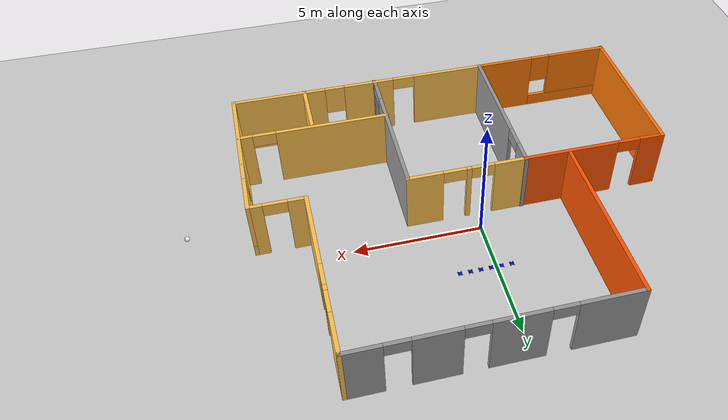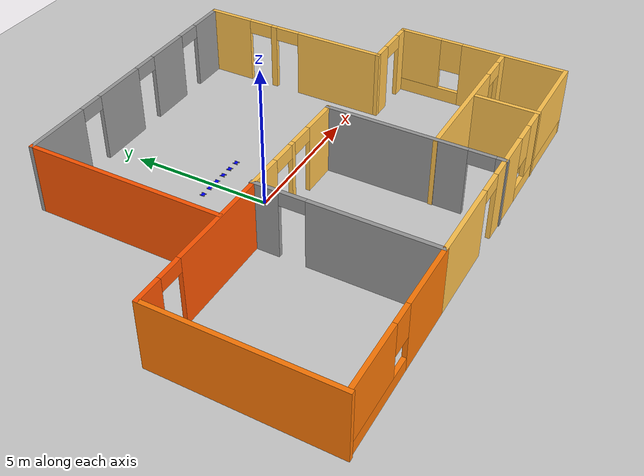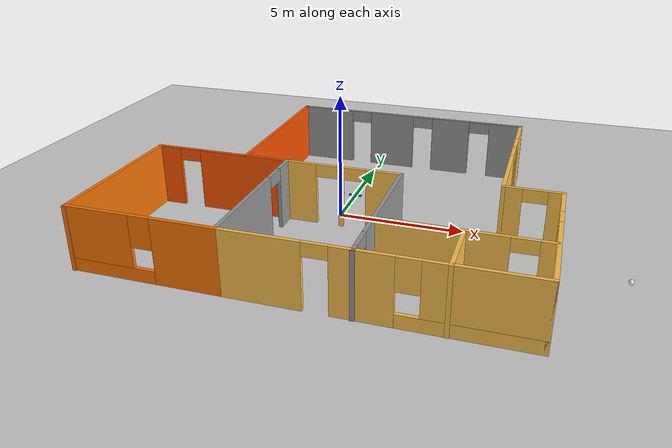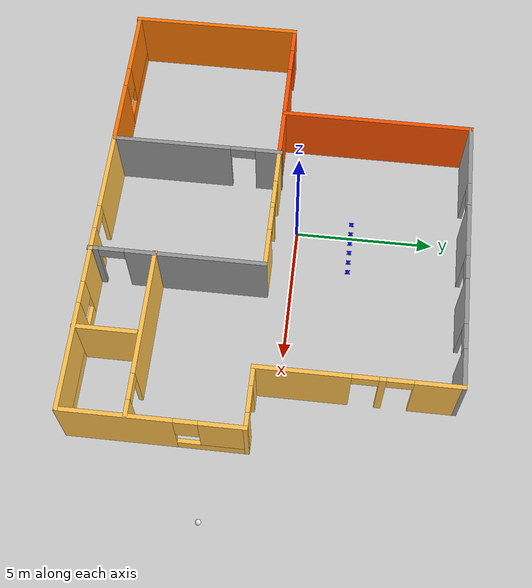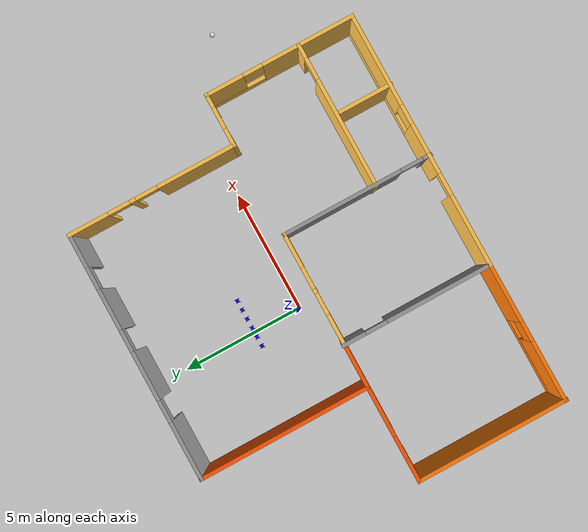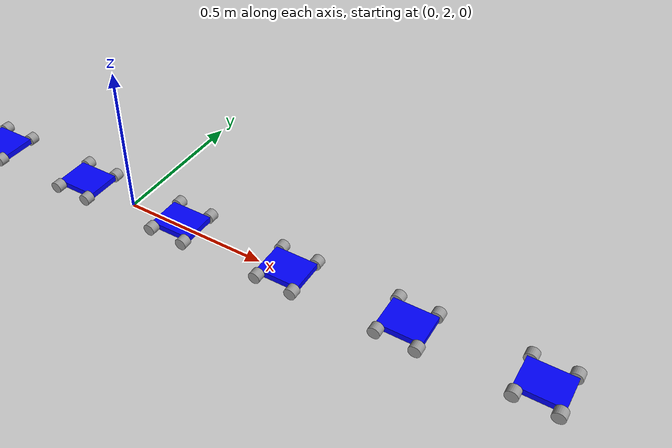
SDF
<sdf version="1.6">
 <world name="default">
  <light name="sun" type="directional">
   <pose>0 0 10 0 -0 0</pose>
   <diffuse>0.8 0.8 0.8 1</diffuse>
   <specular>0.2 0.2 0.2 1</specular>
   <attenuation>
    <range>1000</range>
    <constant>0.9</constant>
    <linear>0.01</linear>
    <quadratic>0.001</quadratic>
   </attenuation>
   <direction>-0.5 0.1 -0.9</direction>
  </light>
  <gravity>0 0 -9.8</gravity>
  <magnetic_field>6e-06 2.3e-05 -4.2e-05</magnetic_field>
  <atmosphere type="adiabatic"/>
  <physics name="default_physics" default="0" type="ode">
   <max_step_size>0.001</max_step_size>
   <real_time_factor>1</real_time_factor>
   <real_time_update_rate>1000</real_time_update_rate>
  </physics>
  <scene><ambient>0.4 0.4 0.4 1</ambient><background>0.7 0.7 0.7 1</background><shadows>1</shadows></scene>
  <spherical_coordinates>
   <surface_model>EARTH_WGS84</surface_model>
   <latitude_deg>0</latitude_deg>
   <longitude_deg>0</longitude_deg>
   <elevation>0</elevation>
   <heading_deg>0</heading_deg>
  </spherical_coordinates>
  <model name="home">
   <pose>0.490005 -0.469645 0 0 -0 0</pose>
   <link name="Wall_29">
    <collision name="Wall_29_Collision">
     <geometry><box><size>6.25 0.15 2.5</size></box></geometry>
     <pose>0 0 1.25 0 -0 0</pose>
    </collision>
    <visual name="Wall_29_Visual">
     <pose>0 0 1.25 0 -0 0</pose>
     <geometry><box><size>6.25 0.15 2.5</size></box></geometry>
     <material>
      <script><uri>file://media/materials/scripts/gazebo.material</uri><name>Gazebo/Grey</name></script>
      <ambient>0.996078 0.47451 0.0196078 1</ambient>
     </material>
     <meta><layer>0</layer></meta>
    </visual>
    <pose>-8.03132 -3.44452 0 0 -0 1.5708</pose>
   </link>
   <link name="Wall_30">
    <pose>-5.23132 -0.394516 0 0 -0 0</pose>
    <visual name="Wall_30_Visual_0">
     <pose>-2.36576 0 1.25 0 -0 0</pose>
     <geometry><box><size>1.01847 0.15 2.5</size></box></geometry>
     <material>
      <script><uri>file://media/materials/scripts/gazebo.material</uri><name>Gazebo/Grey</name></script>
      <ambient>1 0.333333 0 1</ambient>
     </material>
     <meta><layer>0</layer></meta>
    </visual>
    <collision name="Wall_30_Collision_0">
     <geometry><box><size>1.01847 0.15 2.5</size></box></geometry>
     <pose>-2.36576 0 1.25 0 -0 0</pose>
    </collision>
    <visual name="Wall_30_Visual_1">
     <pose>0.959236 0 1.25 0 -0 0</pose>
     <geometry><box><size>3.83153 0.15 2.5</size></box></geometry>
     <material>
      <script><uri>file://media/materials/scripts/gazebo.material</uri><name>Gazebo/Grey</name></script>
      <ambient>1 0.333333 0 1</ambient>
     </material>
     <meta><layer>0</layer></meta>
    </visual>
    <collision name="Wall_30_Collision_1">
     <geometry><box><size>3.83153 0.15 2.5</size></box></geometry>
     <pose>0.959236 0 1.25 0 -0 0</pose>
    </collision>
    <visual name="Wall_30_Visual_2">
     <pose>-1.40653 0 2.25 0 -0 0</pose>
     <geometry><box><size>0.9 0.15 0.5</size></box></geometry>
     <material>
      <script><uri>file://media/materials/scripts/gazebo.material</uri><name>Gazebo/Grey</name></script>
      <ambient>1 0.333333 0 1</ambient>
     </material>
     <meta><layer>0</layer></meta>
    </visual>
    <collision name="Wall_30_Collision_2">
     <geometry><box><size>0.9 0.15 0.5</size></box></geometry>
     <pose>-1.40653 0 2.25 0 -0 0</pose>
    </collision>
   </link>
   <link name="Wall_33">
    <pose>-2.41868 -3.40548 0 0 0 -1.5708</pose>
    <visual name="Wall_33_Visual_0">
     <pose>-2.63049 0 1.25 0 -0 0</pose>
     <geometry><box><size>0.989023 0.15 2.5</size></box></geometry>
     <material>
      <script><uri>file://media/materials/scripts/gazebo.material</uri><name>Gazebo/Grey</name></script>
      <ambient>1 1 1 1</ambient>
     </material>
     <meta><layer>0</layer></meta>
    </visual>
    <collision name="Wall_33_Collision_0">
     <geometry><box><size>0.989023 0.15 2.5</size></box></geometry>
     <pose>-2.63049 0 1.25 0 -0 0</pose>
    </collision>
    <visual name="Wall_33_Visual_1">
     <pose>0.944511 0 1.25 0 -0 0</pose>
     <geometry><box><size>4.36098 0.15 2.5</size></box></geometry>
     <material>
      <script><uri>file://media/materials/scripts/gazebo.material</uri><name>Gazebo/Grey</name></script>
      <ambient>1 1 1 1</ambient>
     </material>
     <meta><layer>0</layer></meta>
    </visual>
    <collision name="Wall_33_Collision_1">
     <geometry><box><size>4.36098 0.15 2.5</size></box></geometry>
     <pose>0.944511 0 1.25 0 -0 0</pose>
    </collision>
    <visual name="Wall_33_Visual_2">
     <pose>-1.68598 0 2.25 0 -0 0</pose>
     <geometry><box><size>0.9 0.15 0.5</size></box></geometry>
     <material>
      <script><uri>file://media/materials/scripts/gazebo.material</uri><name>Gazebo/Grey</name></script>
      <ambient>1 1 1 1</ambient>
     </material>
     <meta><layer>0</layer></meta>
    </visual>
    <collision name="Wall_33_Collision_2">
     <geometry><box><size>0.9 0.15 0.5</size></box></geometry>
     <pose>-1.68598 0 2.25 0 -0 0</pose>
    </collision>
   </link>
   <link name="Wall_34">
    <pose>-5.21868 -6.45548 0 0 -0 3.14159</pose>
    <visual name="Wall_34_Visual_0">
     <pose>-1.65698 0 1.25 0 -0 0</pose>
     <geometry><box><size>2.43604 0.15 2.5</size></box></geometry>
     <material>
      <script><uri>file://media/materials/scripts/gazebo.material</uri><name>Gazebo/Grey</name></script>
      <ambient>0.996078 0.47451 0.0196078 1</ambient>
     </material>
     <meta><layer>0</layer></meta>
    </visual>
    <collision name="Wall_34_Collision_0">
     <geometry><box><size>2.43604 0.15 2.5</size></box></geometry>
     <pose>-1.65698 0 1.25 0 -0 0</pose>
    </collision>
    <visual name="Wall_34_Visual_1">
     <pose>1.21802 0 0.25 0 -0 0</pose>
     <geometry><box><size>3.31396 0.15 0.5</size></box></geometry>
     <material>
      <script><uri>file://media/materials/scripts/gazebo.material</uri><name>Gazebo/Grey</name></script>
      <ambient>0.996078 0.47451 0.0196078 1</ambient>
     </material>
     <meta><layer>0</layer></meta>
    </visual>
    <collision name="Wall_34_Collision_1">
     <geometry><box><size>3.31396 0.15 0.5</size></box></geometry>
     <pose>1.21802 0 0.25 0 -0 0</pose>
    </collision>
    <visual name="Wall_34_Visual_2">
     <pose>1.61802 0 1.5 0 -0 0</pose>
     <geometry><box><size>2.51396 0.15 2</size></box></geometry>
     <material>
      <script><uri>file://media/materials/scripts/gazebo.material</uri><name>Gazebo/Grey</name></script>
      <ambient>0.996078 0.47451 0.0196078 1</ambient>
     </material>
     <meta><layer>0</layer></meta>
    </visual>
    <collision name="Wall_34_Collision_2">
     <geometry><box><size>2.51396 0.15 2</size></box></geometry>
     <pose>1.61802 0 1.5 0 -0 0</pose>
    </collision>
    <visual name="Wall_34_Visual_3">
     <pose>-0.038964 0 1.9 0 -0 0</pose>
     <geometry><box><size>0.8 0.15 1.2</size></box></geometry>
     <material>
      <script><uri>file://media/materials/scripts/gazebo.material</uri><name>Gazebo/Grey</name></script>
      <ambient>0.996078 0.47451 0.0196078 1</ambient>
     </material>
     <meta><layer>0</layer></meta>
    </visual>
    <collision name="Wall_34_Collision_3">
     <geometry><box><size>0.8 0.15 1.2</size></box></geometry>
     <pose>-0.038964 0 1.9 0 -0 0</pose>
    </collision>
   </link>
   <link name="Wall_38">
    <pose>-0.118679 -6.45548 0 0 -0 0</pose>
    <visual name="Wall_38_Visual_0">
     <pose>-0.881556 0 1.25 0 -0 0</pose>
     <geometry><box><size>2.98689 0.15 2.5</size></box></geometry>
     <material>
      <script><uri>file://media/materials/scripts/gazebo.material</uri><name>Gazebo/Grey</name></script>
      <ambient>1 0.764706 0.305882 1</ambient>
     </material>
     <meta><layer>0</layer></meta>
    </visual>
    <collision name="Wall_38_Collision_0">
     <geometry><box><size>2.98689 0.15 2.5</size></box></geometry>
     <pose>-0.881556 0 1.25 0 -0 0</pose>
    </collision>
    <visual name="Wall_38_Visual_1">
     <pose>1.94344 0 1.25 0 -0 0</pose>
     <geometry><box><size>0.863112 0.15 2.5</size></box></geometry>
     <material>
      <script><uri>file://media/materials/scripts/gazebo.material</uri><name>Gazebo/Grey</name></script>
      <ambient>1 0.764706 0.305882 1</ambient>
     </material>
     <meta><layer>0</layer></meta>
    </visual>
    <collision name="Wall_38_Collision_1">
     <geometry><box><size>0.863112 0.15 2.5</size></box></geometry>
     <pose>1.94344 0 1.25 0 -0 0</pose>
    </collision>
    <visual name="Wall_38_Visual_2">
     <pose>1.06189 0 2.25 0 -0 0</pose>
     <geometry><box><size>0.9 0.15 0.5</size></box></geometry>
     <material>
      <script><uri>file://media/materials/scripts/gazebo.material</uri><name>Gazebo/Grey</name></script>
      <ambient>1 0.764706 0.305882 1</ambient>
     </material>
     <meta><layer>0</layer></meta>
    </visual>
    <collision name="Wall_38_Collision_2">
     <geometry><box><size>0.9 0.15 0.5</size></box></geometry>
     <pose>1.06189 0 2.25 0 -0 0</pose>
    </collision>
   </link>
   <link name="Wall_39">
    <pose>5.10632 -6.45548 0 0 -0 0</pose>
    <visual name="Wall_39_Visual_0">
     <pose>-2.31199 0 1.25 0 -0 0</pose>
     <geometry><box><size>1.37601 0.15 2.5</size></box></geometry>
     <material>
      <script><uri>file://media/materials/scripts/gazebo.material</uri><name>Gazebo/Grey</name></script>
      <ambient>1 0.764706 0.305882 1</ambient>
     </material>
     <meta><layer>0</layer></meta>
    </visual>
    <collision name="Wall_39_Collision_0">
     <geometry><box><size>1.37601 0.15 2.5</size></box></geometry>
     <pose>-2.31199 0 1.25 0 -0 0</pose>
    </collision>
    <visual name="Wall_39_Visual_1">
     <pose>0.688007 0 0.25 0 -0 0</pose>
     <geometry><box><size>4.62399 0.15 0.5</size></box></geometry>
     <material>
      <script><uri>file://media/materials/scripts/gazebo.material</uri><name>Gazebo/Grey</name></script>
      <ambient>1 0.764706 0.305882 1</ambient>
     </material>
     <meta><layer>0</layer></meta>
    </visual>
    <collision name="Wall_39_Collision_1">
     <geometry><box><size>4.62399 0.15 0.5</size></box></geometry>
     <pose>0.688007 0 0.25 0 -0 0</pose>
    </collision>
    <visual name="Wall_39_Visual_2">
     <pose>1.08801 0 1.5 0 -0 0</pose>
     <geometry><box><size>3.82399 0.15 2</size></box></geometry>
     <material>
      <script><uri>file://media/materials/scripts/gazebo.material</uri><name>Gazebo/Grey</name></script>
      <ambient>1 0.764706 0.305882 1</ambient>
     </material>
     <meta><layer>0</layer></meta>
    </visual>
    <collision name="Wall_39_Collision_2">
     <geometry><box><size>3.82399 0.15 2</size></box></geometry>
     <pose>1.08801 0 1.5 0 -0 0</pose>
    </collision>
    <visual name="Wall_39_Visual_3">
     <pose>-1.22399 0 1.9 0 -0 0</pose>
     <geometry><box><size>0.8 0.15 1.2</size></box></geometry>
     <material>
      <script><uri>file://media/materials/scripts/gazebo.material</uri><name>Gazebo/Grey</name></script>
      <ambient>1 0.764706 0.305882 1</ambient>
     </material>
     <meta><layer>0</layer></meta>
    </visual>
    <collision name="Wall_39_Collision_3">
     <geometry><box><size>0.8 0.15 1.2</size></box></geometry>
     <pose>-1.22399 0 1.9 0 -0 0</pose>
    </collision>
   </link>
   <link name="Wall_40">
    <pose>8.03132 -3.40548 0 0 -0 1.5708</pose>
    <visual name="Wall_40_Visual_0">
     <pose>-1.2027 0 1.25 0 -0 0</pose>
     <geometry><box><size>3.8446 0.15 2.5</size></box></geometry>
     <material>
      <script><uri>file://media/materials/scripts/gazebo.material</uri><name>Gazebo/Grey</name></script>
      <ambient>1 0.764706 0.305882 1</ambient>
     </material>
     <meta><layer>0</layer></meta>
    </visual>
    <collision name="Wall_40_Collision_0">
     <geometry><box><size>3.8446 0.15 2.5</size></box></geometry>
     <pose>-1.2027 0 1.25 0 -0 0</pose>
    </collision>
    <visual name="Wall_40_Visual_1">
     <pose>1.9223 0 0.25 0 -0 0</pose>
     <geometry><box><size>2.4054 0.15 0.5</size></box></geometry>
     <material>
      <script><uri>file://media/materials/scripts/gazebo.material</uri><name>Gazebo/Grey</name></script>
      <ambient>1 0.764706 0.305882 1</ambient>
     </material>
     <meta><layer>0</layer></meta>
    </visual>
    <collision name="Wall_40_Collision_1">
     <geometry><box><size>2.4054 0.15 0.5</size></box></geometry>
     <pose>1.9223 0 0.25 0 -0 0</pose>
    </collision>
    <visual name="Wall_40_Visual_2">
     <pose>2.3223 0 1.5 0 -0 0</pose>
     <geometry><box><size>1.6054 0.15 2</size></box></geometry>
     <material>
      <script><uri>file://media/materials/scripts/gazebo.material</uri><name>Gazebo/Grey</name></script>
      <ambient>1 0.764706 0.305882 1</ambient>
     </material>
     <meta><layer>0</layer></meta>
    </visual>
    <collision name="Wall_40_Collision_2">
     <geometry><box><size>1.6054 0.15 2</size></box></geometry>
     <pose>2.3223 0 1.5 0 -0 0</pose>
    </collision>
    <visual name="Wall_40_Visual_3">
     <pose>1.1196 0 1.9 0 -0 0</pose>
     <geometry><box><size>0.8 0.15 1.2</size></box></geometry>
     <material>
      <script><uri>file://media/materials/scripts/gazebo.material</uri><name>Gazebo/Grey</name></script>
      <ambient>1 0.764706 0.305882 1</ambient>
     </material>
     <meta><layer>0</layer></meta>
    </visual>
    <collision name="Wall_40_Collision_3">
     <geometry><box><size>0.8 0.15 1.2</size></box></geometry>
     <pose>1.1196 0 1.9 0 -0 0</pose>
    </collision>
   </link>
   <link name="Wall_41">
    <pose>6.98132 -0.355484 0 0 -0 3.14159</pose>
    <visual name="Wall_41_Visual_0">
     <pose>-0.827467 0 1.25 0 -0 0</pose>
     <geometry><box><size>0.595067 0.15 2.5</size></box></geometry>
     <material>
      <script><uri>file://media/materials/scripts/gazebo.material</uri><name>Gazebo/Grey</name></script>
      <ambient>1 0.764706 0.305882 1</ambient>
     </material>
     <meta><layer>0</layer></meta>
    </visual>
    <collision name="Wall_41_Collision_0">
     <geometry><box><size>0.595067 0.15 2.5</size></box></geometry>
     <pose>-0.827467 0 1.25 0 -0 0</pose>
    </collision>
    <visual name="Wall_41_Visual_1">
     <pose>0.747533 0 1.25 0 -0 0</pose>
     <geometry><box><size>0.754933 0.15 2.5</size></box></geometry>
     <material>
      <script><uri>file://media/materials/scripts/gazebo.material</uri><name>Gazebo/Grey</name></script>
      <ambient>1 0.764706 0.305882 1</ambient>
     </material>
     <meta><layer>0</layer></meta>
    </visual>
    <collision name="Wall_41_Collision_1">
     <geometry><box><size>0.754933 0.15 2.5</size></box></geometry>
     <pose>0.747533 0 1.25 0 -0 0</pose>
    </collision>
    <visual name="Wall_41_Visual_2">
     <pose>-0.079933 0 2.25 0 -0 0</pose>
     <geometry><box><size>0.9 0.15 0.5</size></box></geometry>
     <material>
      <script><uri>file://media/materials/scripts/gazebo.material</uri><name>Gazebo/Grey</name></script>
      <ambient>1 0.764706 0.305882 1</ambient>
     </material>
     <meta><layer>0</layer></meta>
    </visual>
    <collision name="Wall_41_Collision_2">
     <geometry><box><size>0.9 0.15 0.5</size></box></geometry>
     <pose>-0.079933 0 2.25 0 -0 0</pose>
    </collision>
   </link>
   <link name="Wall_42">
    <pose>5.93132 3.06952 0 0 -0 1.5708</pose>
    <visual name="Wall_42_Visual_0">
     <pose>-1.86127 0 1.25 0 -0 0</pose>
     <geometry><box><size>3.27747 0.15 2.5</size></box></geometry>
     <material>
      <script><uri>file://media/materials/scripts/gazebo.material</uri><name>Gazebo/Grey</name></script>
      <ambient>1 0.764706 0.305882 1</ambient>
     </material>
     <meta><layer>0</layer></meta>
    </visual>
    <collision name="Wall_42_Collision_0">
     <geometry><box><size>3.27747 0.15 2.5</size></box></geometry>
     <pose>-1.86127 0 1.25 0 -0 0</pose>
    </collision>
    <visual name="Wall_42_Visual_1">
     <pose>0.793847 0 1.25 0 -0 0</pose>
     <geometry><box><size>0.232756 0.15 2.5</size></box></geometry>
     <material>
      <script><uri>file://media/materials/scripts/gazebo.material</uri><name>Gazebo/Grey</name></script>
      <ambient>1 0.764706 0.305882 1</ambient>
     </material>
     <meta><layer>0</layer></meta>
    </visual>
    <collision name="Wall_42_Collision_1">
     <geometry><box><size>0.232756 0.15 2.5</size></box></geometry>
     <pose>0.793847 0 1.25 0 -0 0</pose>
    </collision>
    <visual name="Wall_42_Visual_2">
     <pose>2.65511 0 1.25 0 -0 0</pose>
     <geometry><box><size>1.68978 0.15 2.5</size></box></geometry>
     <material>
      <script><uri>file://media/materials/scripts/gazebo.material</uri><name>Gazebo/Grey</name></script>
      <ambient>1 0.764706 0.305882 1</ambient>
     </material>
     <meta><layer>0</layer></meta>
    </visual>
    <collision name="Wall_42_Collision_2">
     <geometry><box><size>1.68978 0.15 2.5</size></box></geometry>
     <pose>2.65511 0 1.25 0 -0 0</pose>
    </collision>
    <visual name="Wall_42_Visual_3">
     <pose>0.227469 0 2.25 0 -0 0</pose>
     <geometry><box><size>0.9 0.15 0.5</size></box></geometry>
     <material>
      <script><uri>file://media/materials/scripts/gazebo.material</uri><name>Gazebo/Grey</name></script>
      <ambient>1 0.764706 0.305882 1</ambient>
     </material>
     <meta><layer>0</layer></meta>
    </visual>
    <collision name="Wall_42_Collision_3">
     <geometry><box><size>0.9 0.15 0.5</size></box></geometry>
     <pose>0.227469 0 2.25 0 -0 0</pose>
    </collision>
    <visual name="Wall_42_Visual_4">
     <pose>1.36023 0 2.25 0 -0 0</pose>
     <geometry><box><size>0.9 0.15 0.5</size></box></geometry>
     <material>
      <script><uri>file://media/materials/scripts/gazebo.material</uri><name>Gazebo/Grey</name></script>
      <ambient>1 0.764706 0.305882 1</ambient>
     </material>
     <meta><layer>0</layer></meta>
    </visual>
    <collision name="Wall_42_Collision_4">
     <geometry><box><size>0.9 0.15 0.5</size></box></geometry>
     <pose>1.36023 0 2.25 0 -0 0</pose>
    </collision>
   </link>
   <link name="Wall_43">
    <pose>0.881321 6.49452 0 0 -0 3.14159</pose>
    <visual name="Wall_43_Visual_0">
     <pose>-4.40937 0 1.25 0 -0 0</pose>
     <geometry><box><size>1.43125 0.15 2.5</size></box></geometry>
     <material>
      <script><uri>file://media/materials/scripts/gazebo.material</uri><name>Gazebo/Grey</name></script>
      <ambient>1 1 1 1</ambient>
     </material>
     <meta><layer>0</layer></meta>
    </visual>
    <collision name="Wall_43_Collision_0">
     <geometry><box><size>1.43125 0.15 2.5</size></box></geometry>
     <pose>-4.40937 0 1.25 0 -0 0</pose>
    </collision>
    <visual name="Wall_43_Visual_1">
     <pose>-1.94917 0 1.25 0 -0 0</pose>
     <geometry><box><size>1.68916 0.15 2.5</size></box></geometry>
     <material>
      <script><uri>file://media/materials/scripts/gazebo.material</uri><name>Gazebo/Grey</name></script>
      <ambient>1 1 1 1</ambient>
     </material>
     <meta><layer>0</layer></meta>
    </visual>
    <collision name="Wall_43_Collision_1">
     <geometry><box><size>1.68916 0.15 2.5</size></box></geometry>
     <pose>-1.94917 0 1.25 0 -0 0</pose>
    </collision>
    <visual name="Wall_43_Visual_2">
     <pose>0.801811 0 1.25 0 -0 0</pose>
     <geometry><box><size>2.0128 0.15 2.5</size></box></geometry>
     <material>
      <script><uri>file://media/materials/scripts/gazebo.material</uri><name>Gazebo/Grey</name></script>
      <ambient>1 1 1 1</ambient>
     </material>
     <meta><layer>0</layer></meta>
    </visual>
    <collision name="Wall_43_Collision_2">
     <geometry><box><size>2.0128 0.15 2.5</size></box></geometry>
     <pose>0.801811 0 1.25 0 -0 0</pose>
    </collision>
    <visual name="Wall_43_Visual_3">
     <pose>3.91661 0 1.25 0 -0 0</pose>
     <geometry><box><size>2.41679 0.15 2.5</size></box></geometry>
     <material>
      <script><uri>file://media/materials/scripts/gazebo.material</uri><name>Gazebo/Grey</name></script>
      <ambient>1 1 1 1</ambient>
     </material>
     <meta><layer>0</layer></meta>
    </visual>
    <collision name="Wall_43_Collision_3">
     <geometry><box><size>2.41679 0.15 2.5</size></box></geometry>
     <pose>3.91661 0 1.25 0 -0 0</pose>
    </collision>
    <visual name="Wall_43_Visual_4">
     <pose>-3.24375 0 2.25 0 -0 0</pose>
     <geometry><box><size>0.9 0.15 0.5</size></box></geometry>
     <material>
      <script><uri>file://media/materials/scripts/gazebo.material</uri><name>Gazebo/Grey</name></script>
      <ambient>1 1 1 1</ambient>
     </material>
     <meta><layer>0</layer></meta>
    </visual>
    <collision name="Wall_43_Collision_4">
     <geometry><box><size>0.9 0.15 0.5</size></box></geometry>
     <pose>-3.24375 0 2.25 0 -0 0</pose>
    </collision>
    <visual name="Wall_43_Visual_5">
     <pose>-0.654589 0 2.25 0 -0 0</pose>
     <geometry><box><size>0.9 0.15 0.5</size></box></geometry>
     <material>
      <script><uri>file://media/materials/scripts/gazebo.material</uri><name>Gazebo/Grey</name></script>
      <ambient>1 1 1 1</ambient>
     </material>
     <meta><layer>0</layer></meta>
    </visual>
    <collision name="Wall_43_Collision_5">
     <geometry><box><size>0.9 0.15 0.5</size></box></geometry>
     <pose>-0.654589 0 2.25 0 -0 0</pose>
    </collision>
    <visual name="Wall_43_Visual_6">
     <pose>2.25821 0 2.25 0 -0 0</pose>
     <geometry><box><size>0.9 0.15 0.5</size></box></geometry>
     <material>
      <script><uri>file://media/materials/scripts/gazebo.material</uri><name>Gazebo/Grey</name></script>
      <ambient>1 1 1 1</ambient>
     </material>
     <meta><layer>0</layer></meta>
    </visual>
    <collision name="Wall_43_Collision_6">
     <geometry><box><size>0.9 0.15 0.5</size></box></geometry>
     <pose>2.25821 0 2.25 0 -0 0</pose>
    </collision>
   </link>
   <link name="Wall_44">
    <collision name="Wall_44_Collision">
     <geometry><box><size>7 0.15 2.5</size></box></geometry>
     <pose>0 0 1.25 0 -0 0</pose>
    </collision>
    <visual name="Wall_44_Visual">
     <pose>0 0 1.25 0 -0 0</pose>
     <geometry><box><size>7 0.15 2.5</size></box></geometry>
     <material>
      <script><uri>file://media/materials/scripts/gazebo.material</uri><name>Gazebo/Grey</name></script>
      <ambient>1 0.333333 0 1</ambient>
     </material>
     <meta><layer>0</layer></meta>
    </visual>
    <pose>-4.16868 3.06952 0 0 0 -1.5708</pose>
   </link>
   <link name="Wall_46">
    <pose>-0.131321 -0.394516 0 0 -0 0</pose>
    <visual name="Wall_46_Visual_0">
     <pose>-1.71314 0 1.25 0 -0 0</pose>
     <geometry><box><size>1.32372 0.15 2.5</size></box></geometry>
     <material>
      <script><uri>file://media/materials/scripts/gazebo.material</uri><name>Gazebo/Grey</name></script>
      <ambient>1 0.764706 0.305882 1</ambient>
     </material>
     <meta><layer>0</layer></meta>
    </visual>
    <collision name="Wall_46_Collision_0">
     <geometry><box><size>1.32372 0.15 2.5</size></box></geometry>
     <pose>-1.71314 0 1.25 0 -0 0</pose>
    </collision>
    <visual name="Wall_46_Visual_1">
     <pose>-0.055979 0 1.25 0 -0 0</pose>
     <geometry><box><size>0.190608 0.15 2.5</size></box></geometry>
     <material>
      <script><uri>file://media/materials/scripts/gazebo.material</uri><name>Gazebo/Grey</name></script>
      <ambient>1 0.764706 0.305882 1</ambient>
     </material>
     <meta><layer>0</layer></meta>
    </visual>
    <collision name="Wall_46_Collision_1">
     <geometry><box><size>0.190608 0.15 2.5</size></box></geometry>
     <pose>-0.055979 0 1.25 0 -0 0</pose>
    </collision>
    <visual name="Wall_46_Visual_2">
     <pose>1.65716 0 1.25 0 -0 0</pose>
     <geometry><box><size>1.43568 0.15 2.5</size></box></geometry>
     <material>
      <script><uri>file://media/materials/scripts/gazebo.material</uri><name>Gazebo/Grey</name></script>
      <ambient>1 0.764706 0.305882 1</ambient>
     </material>
     <meta><layer>0</layer></meta>
    </visual>
    <collision name="Wall_46_Collision_2">
     <geometry><box><size>1.43568 0.15 2.5</size></box></geometry>
     <pose>1.65716 0 1.25 0 -0 0</pose>
    </collision>
    <visual name="Wall_46_Visual_3">
     <pose>-0.601283 0 2.25 0 -0 0</pose>
     <geometry><box><size>0.9 0.15 0.5</size></box></geometry>
     <material>
      <script><uri>file://media/materials/scripts/gazebo.material</uri><name>Gazebo/Grey</name></script>
      <ambient>1 0.764706 0.305882 1</ambient>
     </material>
     <meta><layer>0</layer></meta>
    </visual>
    <collision name="Wall_46_Collision_3">
     <geometry><box><size>0.9 0.15 0.5</size></box></geometry>
     <pose>-0.601283 0 2.25 0 -0 0</pose>
    </collision>
    <visual name="Wall_46_Visual_4">
     <pose>0.489325 0 2.25 0 -0 0</pose>
     <geometry><box><size>0.9 0.15 0.5</size></box></geometry>
     <material>
      <script><uri>file://media/materials/scripts/gazebo.material</uri><name>Gazebo/Grey</name></script>
      <ambient>1 0.764706 0.305882 1</ambient>
     </material>
     <meta><layer>0</layer></meta>
    </visual>
    <collision name="Wall_46_Collision_4">
     <geometry><box><size>0.9 0.15 0.5</size></box></geometry>
     <pose>0.489325 0 2.25 0 -0 0</pose>
    </collision>
   </link>
   <link name="Wall_47">
    <pose>2.16868 -3.44452 0 0 0 -1.5708</pose>
    <visual name="Wall_47_Visual_0">
     <pose>-0.645037 0 1.25 0 -0 0</pose>
     <geometry><box><size>4.95993 0.15 2.5</size></box></geometry>
     <material>
      <script><uri>file://media/materials/scripts/gazebo.material</uri><name>Gazebo/Grey</name></script>
      <ambient>1 1 1 1</ambient>
     </material>
     <meta><layer>0</layer></meta>
    </visual>
    <collision name="Wall_47_Collision_0">
     <geometry><box><size>4.95993 0.15 2.5</size></box></geometry>
     <pose>-0.645037 0 1.25 0 -0 0</pose>
    </collision>
    <visual name="Wall_47_Visual_1">
     <pose>2.92996 0 1.25 0 -0 0</pose>
     <geometry><box><size>0.390074 0.15 2.5</size></box></geometry>
     <material>
      <script><uri>file://media/materials/scripts/gazebo.material</uri><name>Gazebo/Grey</name></script>
      <ambient>1 1 1 1</ambient>
     </material>
     <meta><layer>0</layer></meta>
    </visual>
    <collision name="Wall_47_Collision_1">
     <geometry><box><size>0.390074 0.15 2.5</size></box></geometry>
     <pose>2.92996 0 1.25 0 -0 0</pose>
    </collision>
    <visual name="Wall_47_Visual_2">
     <pose>2.28493 0 2.25 0 -0 0</pose>
     <geometry><box><size>0.9 0.15 0.5</size></box></geometry>
     <material>
      <script><uri>file://media/materials/scripts/gazebo.material</uri><name>Gazebo/Grey</name></script>
      <ambient>1 1 1 1</ambient>
     </material>
     <meta><layer>0</layer></meta>
    </visual>
    <collision name="Wall_47_Collision_2">
     <geometry><box><size>0.9 0.15 0.5</size></box></geometry>
     <pose>2.28493 0 2.25 0 -0 0</pose>
    </collision>
   </link>
   <link name="Wall_49">
    <pose>5.06537 -4.21229 0 0 -0 0</pose>
    <visual name="Wall_49_Visual_0">
     <pose>-0.740357 0 1.25 0 -0 0</pose>
     <geometry><box><size>4.51929 0.15 2.5</size></box></geometry>
     <material>
      <script><uri>file://media/materials/scripts/gazebo.material</uri><name>Gazebo/Grey</name></script>
      <ambient>1 0.764706 0.305882 1</ambient>
     </material>
     <meta><layer>0</layer></meta>
    </visual>
    <collision name="Wall_49_Collision_0">
     <geometry><box><size>4.51929 0.15 2.5</size></box></geometry>
     <pose>-0.740357 0 1.25 0 -0 0</pose>
    </collision>
    <visual name="Wall_49_Visual_1">
     <pose>2.70964 0 1.25 0 -0 0</pose>
     <geometry><box><size>0.580713 0.15 2.5</size></box></geometry>
     <material>
      <script><uri>file://media/materials/scripts/gazebo.material</uri><name>Gazebo/Grey</name></script>
      <ambient>1 0.764706 0.305882 1</ambient>
     </material>
     <meta><layer>0</layer></meta>
    </visual>
    <collision name="Wall_49_Collision_1">
     <geometry><box><size>0.580713 0.15 2.5</size></box></geometry>
     <pose>2.70964 0 1.25 0 -0 0</pose>
    </collision>
    <visual name="Wall_49_Visual_2">
     <pose>1.96929 0 2.25 0 -0 0</pose>
     <geometry><box><size>0.9 0.15 0.5</size></box></geometry>
     <material>
      <script><uri>file://media/materials/scripts/gazebo.material</uri><name>Gazebo/Grey</name></script>
      <ambient>1 0.764706 0.305882 1</ambient>
     </material>
     <meta><layer>0</layer></meta>
    </visual>
    <collision name="Wall_49_Collision_2">
     <geometry><box><size>0.9 0.15 0.5</size></box></geometry>
     <pose>1.96929 0 2.25 0 -0 0</pose>
    </collision>
   </link>
   <link name="Wall_51">
    <collision name="Wall_51_Collision">
     <geometry><box><size>2.25 0.15 2.5</size></box></geometry>
     <pose>0 0 1.25 0 -0 0</pose>
    </collision>
    <visual name="Wall_51_Visual">
     <pose>0 0 1.25 0 -0 0</pose>
     <geometry><box><size>2.25 0.15 2.5</size></box></geometry>
     <material>
      <script><uri>file://media/materials/scripts/gazebo.material</uri><name>Gazebo/Grey</name></script>
      <ambient>1 0.764706 0.305882 1</ambient>
     </material>
     <meta><layer>0</layer></meta>
    </visual>
    <pose>5.13408 -5.42411 0 0 0 -1.5708</pose>
   </link>
   <static>1</static>
  </model>
  <model name="ground_plane">
   <static>1</static>
   <link name="link">
    <collision name="collision">
     <geometry><plane><normal>0 0 1</normal><size>100 100</size></plane></geometry>
     <surface><friction><ode><mu>100</mu><mu2>50</mu2></ode></friction></surface>
    </collision>
    <visual name="visual">
     <cast_shadows>0</cast_shadows>
     <geometry><plane><normal>0 0 1</normal><size>100 100</size></plane></geometry>
     <material>
      <script><uri>file://media/materials/scripts/gazebo.material</uri><name>Gazebo/Grey</name></script>
     </material>
    </visual>
   </link>
  </model>
  <model name="nanocrawler1">
   <link name="chassis">
    <inertial>
     <mass>1</mass>
     <inertia>
      <ixx>0.166667</ixx>
      <ixy>0</ixy>
      <ixz>0</ixz>
      <iyy>0.166667</iyy>
      <iyz>0</iyz>
      <izz>0.166667</izz>
     </inertia>
    </inertial>
    <visual name="visual">
     <geometry><box><size>0.145 0.115 0.02</size></box></geometry>
     <material>
      <lighting>1</lighting>
      <script><uri>file://media/materials/scripts/gazebo.material</uri><name>Gazebo/Grey</name></script>
      <shader type="pixel"><normal_map>__default__</normal_map></shader>
      <ambient>0 0 1 1</ambient>
      <diffuse>0.7 0.7 0.7 1</diffuse>
      <specular>0.01 0.01 0.01 1</specular>
      <emissive>0 0 0 1</emissive>
     </material>
    </visual>
    <collision name="collision">
     <geometry><box><size>0.145 0.115 0.02</size></box></geometry>
     <surface>
      <friction>
       <ode><mu>1</mu><mu2>1</mu2><fdir1>0 0 0</fdir1><slip1>0</slip1><slip2>0</slip2></ode>
       <torsional>
        <coefficient>1</coefficient>
        <patch_radius>0</patch_radius>
        <surface_radius>0</surface_radius>
        <use_patch_radius>1</use_patch_radius>
        <ode><slip>0</slip></ode>
       </torsional>
      </friction>
      <bounce><restitution_coefficient>0</restitution_coefficient><threshold>1e+06</threshold></bounce>
      <contact>
       <collide_without_contact>0</collide_without_contact>
       <collide_without_contact_bitmask>1</collide_without_contact_bitmask>
       <collide_bitmask>1</collide_bitmask>
       <ode>
        <soft_cfm>0</soft_cfm>
        <soft_erp>0.2</soft_erp>
        <kp>1e+13</kp>
        <kd>1</kd>
        <max_vel>0.01</max_vel>
        <min_depth>0</min_depth>
       </ode>
       <bullet>
        <split_impulse>1</split_impulse>
        <split_impulse_penetration_threshold>-0.01</split_impulse_penetration_threshold>
        <soft_cfm>0</soft_cfm>
        <soft_erp>0.2</soft_erp>
        <kp>1e+13</kp>
        <kd>1</kd>
       </bullet>
      </contact>
     </surface>
    </collision>
   </link>
   <link name="left_front_wheel">
    <pose>0.0625 0.0725 0 1.5708 -0 0</pose>
    <inertial>
     <mass>1</mass>
     <inertia><ixx>0.145833</ixx><ixy>0</ixy><ixz>0</ixz><iyy>0.145833</iyy><iyz>0</iyz><izz>0.125</izz></inertia>
    </inertial>
    <visual name="visual">
     <geometry><cylinder><radius>0.02</radius><length>0.03</length></cylinder></geometry>
     <material>
      <lighting>1</lighting>
      <script><uri>file://media/materials/scripts/gazebo.material</uri><name>Gazebo/Grey</name></script>
      <shader type="pixel"><normal_map>__default__</normal_map></shader>
      <ambient>0.1 0.1 0.1 1</ambient>
      <diffuse>0.7 0.7 0.7 1</diffuse>
      <specular>0.01 0.01 0.01 1</specular>
      <emissive>0 0 0 1</emissive>
     </material>
    </visual>
    <collision name="collision">
     <geometry><cylinder><radius>0.02</radius><length>0.03</length></cylinder></geometry>
     <surface>
      <friction>
       <ode><mu>1</mu><mu2>1</mu2><fdir1>0 0 0</fdir1><slip1>0</slip1><slip2>0</slip2></ode>
       <torsional>
        <coefficient>1</coefficient>
        <patch_radius>0</patch_radius>
        <surface_radius>0</surface_radius>
        <use_patch_radius>1</use_patch_radius>
        <ode><slip>0</slip></ode>
       </torsional>
      </friction>
      <bounce><restitution_coefficient>0</restitution_coefficient><threshold>1e+06</threshold></bounce>
      <contact>
       <collide_without_contact>0</collide_without_contact>
       <collide_without_contact_bitmask>1</collide_without_contact_bitmask>
       <collide_bitmask>1</collide_bitmask>
       <ode>
        <soft_cfm>0</soft_cfm>
        <soft_erp>0.2</soft_erp>
        <kp>1e+13</kp>
        <kd>1</kd>
        <max_vel>0.01</max_vel>
        <min_depth>0</min_depth>
       </ode>
       <bullet>
        <split_impulse>1</split_impulse>
        <split_impulse_penetration_threshold>-0.01</split_impulse_penetration_threshold>
        <soft_cfm>0</soft_cfm>
        <soft_erp>0.2</soft_erp>
        <kp>1e+13</kp>
        <kd>1</kd>
       </bullet>
      </contact>
     </surface>
    </collision>
   </link>
   <joint name="left_front_wheel_hinge" type="revolute">
    <child>left_front_wheel</child>
    <parent>chassis</parent>
    <axis>
     <xyz>0 0 1</xyz>
     <use_parent_model_frame>0</use_parent_model_frame>
     <limit><lower>-1e+16</lower><upper>1e+16</upper></limit>
     <dynamics><spring_reference>0</spring_reference><spring_stiffness>0</spring_stiffness></dynamics>
    </axis>
   </joint>
   <link name="right_front_wheel">
    <pose>0.0625 -0.0725 0 1.5708 -0 0</pose>
    <inertial>
     <mass>1</mass>
     <inertia><ixx>0.145833</ixx><ixy>0</ixy><ixz>0</ixz><iyy>0.145833</iyy><iyz>0</iyz><izz>0.125</izz></inertia>
    </inertial>
    <visual name="visual">
     <geometry><cylinder><radius>0.02</radius><length>0.03</length></cylinder></geometry>
     <material>
      <lighting>1</lighting>
      <script><uri>file://media/materials/scripts/gazebo.material</uri><name>Gazebo/Grey</name></script>
      <shader type="pixel"><normal_map>__default__</normal_map></shader>
      <ambient>0.1 0.1 0.1 1</ambient>
      <diffuse>0.7 0.7 0.7 1</diffuse>
      <specular>0.01 0.01 0.01 1</specular>
      <emissive>0 0 0 1</emissive>
     </material>
    </visual>
    <collision name="collision">
     <geometry><cylinder><radius>0.02</radius><length>0.03</length></cylinder></geometry>
     <surface>
      <friction>
       <ode><mu>1</mu><mu2>1</mu2><fdir1>0 0 0</fdir1><slip1>0</slip1><slip2>0</slip2></ode>
       <torsional>
        <coefficient>1</coefficient>
        <patch_radius>0</patch_radius>
        <surface_radius>0</surface_radius>
        <use_patch_radius>1</use_patch_radius>
        <ode><slip>0</slip></ode>
       </torsional>
      </friction>
      <bounce><restitution_coefficient>0</restitution_coefficient><threshold>1e+06</threshold></bounce>
      <contact>
       <collide_without_contact>0</collide_without_contact>
       <collide_without_contact_bitmask>1</collide_without_contact_bitmask>
       <collide_bitmask>1</collide_bitmask>
       <ode>
        <soft_cfm>0</soft_cfm>
        <soft_erp>0.2</soft_erp>
        <kp>1e+13</kp>
        <kd>1</kd>
        <max_vel>0.01</max_vel>
        <min_depth>0</min_depth>
       </ode>
       <bullet>
        <split_impulse>1</split_impulse>
        <split_impulse_penetration_threshold>-0.01</split_impulse_penetration_threshold>
        <soft_cfm>0</soft_cfm>
        <soft_erp>0.2</soft_erp>
        <kp>1e+13</kp>
        <kd>1</kd>
       </bullet>
      </contact>
     </surface>
    </collision>
   </link>
   <joint name="right_front_wheel_hinge" type="revolute">
    <child>right_front_wheel</child>
    <parent>chassis</parent>
    <axis>
     <xyz>0 0 1</xyz>
     <use_parent_model_frame>0</use_parent_model_frame>
     <limit><lower>-1e+16</lower><upper>1e+16</upper></limit>
     <dynamics><spring_reference>0</spring_reference><spring_stiffness>0</spring_stiffness></dynamics>
    </axis>
   </joint>
   <link name="left_rear_wheel">
    <pose>-0.0625 0.0725 0 1.5708 -0 0</pose>
    <inertial>
     <mass>1</mass>
     <inertia><ixx>0.145833</ixx><ixy>0</ixy><ixz>0</ixz><iyy>0.145833</iyy><iyz>0</iyz><izz>0.125</izz></inertia>
    </inertial>
    <visual name="visual">
     <geometry><cylinder><radius>0.02</radius><length>0.03</length></cylinder></geometry>
     <material>
      <lighting>1</lighting>
      <script><uri>file://media/materials/scripts/gazebo.material</uri><name>Gazebo/Grey</name></script>
      <shader type="pixel"><normal_map>__default__</normal_map></shader>
      <ambient>0.1 0.1 0.1 1</ambient>
      <diffuse>0.7 0.7 0.7 1</diffuse>
      <specular>0.01 0.01 0.01 1</specular>
      <emissive>0 0 0 1</emissive>
     </material>
    </visual>
    <collision name="collision">
     <geometry><cylinder><radius>0.02</radius><length>0.03</length></cylinder></geometry>
     <surface>
      <friction>
       <ode><mu>1</mu><mu2>1</mu2><fdir1>0 0 0</fdir1><slip1>0</slip1><slip2>0</slip2></ode>
       <torsional>
        <coefficient>1</coefficient>
        <patch_radius>0</patch_radius>
        <surface_radius>0</surface_radius>
        <use_patch_radius>1</use_patch_radius>
        <ode><slip>0</slip></ode>
       </torsional>
      </friction>
      <bounce><restitution_coefficient>0</restitution_coefficient><threshold>1e+06</threshold></bounce>
      <contact>
       <collide_without_contact>0</collide_without_contact>
       <collide_without_contact_bitmask>1</collide_without_contact_bitmask>
       <collide_bitmask>1</collide_bitmask>
       <ode>
        <soft_cfm>0</soft_cfm>
        <soft_erp>0.2</soft_erp>
        <kp>1e+13</kp>
        <kd>1</kd>
        <max_vel>0.01</max_vel>
        <min_depth>0</min_depth>
       </ode>
       <bullet>
        <split_impulse>1</split_impulse>
        <split_impulse_penetration_threshold>-0.01</split_impulse_penetration_threshold>
        <soft_cfm>0</soft_cfm>
        <soft_erp>0.2</soft_erp>
        <kp>1e+13</kp>
        <kd>1</kd>
       </bullet>
      </contact>
     </surface>
    </collision>
   </link>
   <joint name="left_rear_wheel_hinge" type="revolute">
    <child>left_rear_wheel</child>
    <parent>chassis</parent>
    <axis>
     <xyz>0 0 1</xyz>
     <use_parent_model_frame>0</use_parent_model_frame>
     <limit><lower>-1e+16</lower><upper>1e+16</upper></limit>
     <dynamics><spring_reference>0</spring_reference><spring_stiffness>0</spring_stiffness></dynamics>
    </axis>
   </joint>
   <link name="right_rear_wheel">
    <pose>-0.0625 -0.0725 0 1.5708 -0 0</pose>
    <inertial>
     <mass>1</mass>
     <inertia><ixx>0.145833</ixx><ixy>0</ixy><ixz>0</ixz><iyy>0.145833</iyy><iyz>0</iyz><izz>0.125</izz></inertia>
    </inertial>
    <visual name="visual">
     <geometry><cylinder><radius>0.02</radius><length>0.03</length></cylinder></geometry>
     <material>
      <lighting>1</lighting>
      <script><uri>file://media/materials/scripts/gazebo.material</uri><name>Gazebo/Grey</name></script>
      <shader type="pixel"><normal_map>__default__</normal_map></shader>
      <ambient>0.1 0.1 0.1 1</ambient>
      <diffuse>0.7 0.7 0.7 1</diffuse>
      <specular>0.01 0.01 0.01 1</specular>
      <emissive>0 0 0 1</emissive>
     </material>
    </visual>
    <collision name="collision">
     <geometry><cylinder><radius>0.02</radius><length>0.03</length></cylinder></geometry>
     <surface>
      <friction>
       <ode><mu>1</mu><mu2>1</mu2><fdir1>0 0 0</fdir1><slip1>0</slip1><slip2>0</slip2></ode>
       <torsional>
        <coefficient>1</coefficient>
        <patch_radius>0</patch_radius>
        <surface_radius>0</surface_radius>
        <use_patch_radius>1</use_patch_radius>
        <ode><slip>0</slip></ode>
       </torsional>
      </friction>
      <bounce><restitution_coefficient>0</restitution_coefficient><threshold>1e+06</threshold></bounce>
      <contact>
       <collide_without_contact>0</collide_without_contact>
       <collide_without_contact_bitmask>1</collide_without_contact_bitmask>
       <collide_bitmask>1</collide_bitmask>
       <ode>
        <soft_cfm>0</soft_cfm>
        <soft_erp>0.2</soft_erp>
        <kp>1e+13</kp>
        <kd>1</kd>
        <max_vel>0.01</max_vel>
        <min_depth>0</min_depth>
       </ode>
       <bullet>
        <split_impulse>1</split_impulse>
        <split_impulse_penetration_threshold>-0.01</split_impulse_penetration_threshold>
        <soft_cfm>0</soft_cfm>
        <soft_erp>0.2</soft_erp>
        <kp>1e+13</kp>
        <kd>1</kd>
       </bullet>
      </contact>
     </surface>
    </collision>
   </link>
   <joint name="right_rear_wheel_hinge" type="revolute">
    <child>right_rear_wheel</child>
    <parent>chassis</parent>
    <axis>
     <xyz>0 0 1</xyz>
     <use_parent_model_frame>0</use_parent_model_frame>
     <limit><lower>-1e+16</lower><upper>1e+16</upper></limit>
     <dynamics><spring_reference>0</spring_reference><spring_stiffness>0</spring_stiffness></dynamics>
    </axis>
   </joint>
   <static>0</static>
   <pose>-0.600256 2.0001 0.02 -1e-06 2e-06 -0.000482</pose>
  </model>
  <model name="nanocrawler2">
   <link name="chassis">
    <inertial>
     <mass>1</mass>
     <inertia>
      <ixx>0.166667</ixx>
      <ixy>0</ixy>
      <ixz>0</ixz>
      <iyy>0.166667</iyy>
      <iyz>0</iyz>
      <izz>0.166667</izz>
     </inertia>
    </inertial>
    <visual name="visual">
     <geometry><box><size>0.145 0.115 0.02</size></box></geometry>
     <material>
      <lighting>1</lighting>
      <script><uri>file://media/materials/scripts/gazebo.material</uri><name>Gazebo/Grey</name></script>
      <shader type="pixel"><normal_map>__default__</normal_map></shader>
      <ambient>0 0 1 1</ambient>
      <diffuse>0.7 0.7 0.7 1</diffuse>
      <specular>0.01 0.01 0.01 1</specular>
      <emissive>0 0 0 1</emissive>
     </material>
    </visual>
    <collision name="collision">
     <geometry><box><size>0.145 0.115 0.02</size></box></geometry>
     <surface>
      <friction>
       <ode><mu>1</mu><mu2>1</mu2><fdir1>0 0 0</fdir1><slip1>0</slip1><slip2>0</slip2></ode>
       <torsional>
        <coefficient>1</coefficient>
        <patch_radius>0</patch_radius>
        <surface_radius>0</surface_radius>
        <use_patch_radius>1</use_patch_radius>
        <ode><slip>0</slip></ode>
       </torsional>
      </friction>
      <bounce><restitution_coefficient>0</restitution_coefficient><threshold>1e+06</threshold></bounce>
      <contact>
       <collide_without_contact>0</collide_without_contact>
       <collide_without_contact_bitmask>1</collide_without_contact_bitmask>
       <collide_bitmask>1</collide_bitmask>
       <ode>
        <soft_cfm>0</soft_cfm>
        <soft_erp>0.2</soft_erp>
        <kp>1e+13</kp>
        <kd>1</kd>
        <max_vel>0.01</max_vel>
        <min_depth>0</min_depth>
       </ode>
       <bullet>
        <split_impulse>1</split_impulse>
        <split_impulse_penetration_threshold>-0.01</split_impulse_penetration_threshold>
        <soft_cfm>0</soft_cfm>
        <soft_erp>0.2</soft_erp>
        <kp>1e+13</kp>
        <kd>1</kd>
       </bullet>
      </contact>
     </surface>
    </collision>
   </link>
   <link name="left_front_wheel">
    <pose>0.0625 0.0725 0 1.5708 -0 0</pose>
    <inertial>
     <mass>1</mass>
     <inertia><ixx>0.145833</ixx><ixy>0</ixy><ixz>0</ixz><iyy>0.145833</iyy><iyz>0</iyz><izz>0.125</izz></inertia>
    </inertial>
    <visual name="visual">
     <geometry><cylinder><radius>0.02</radius><length>0.03</length></cylinder></geometry>
     <material>
      <lighting>1</lighting>
      <script><uri>file://media/materials/scripts/gazebo.material</uri><name>Gazebo/Grey</name></script>
      <shader type="pixel"><normal_map>__default__</normal_map></shader>
      <ambient>0.1 0.1 0.1 1</ambient>
      <diffuse>0.7 0.7 0.7 1</diffuse>
      <specular>0.01 0.01 0.01 1</specular>
      <emissive>0 0 0 1</emissive>
     </material>
    </visual>
    <collision name="collision">
     <geometry><cylinder><radius>0.02</radius><length>0.03</length></cylinder></geometry>
     <surface>
      <friction>
       <ode><mu>1</mu><mu2>1</mu2><fdir1>0 0 0</fdir1><slip1>0</slip1><slip2>0</slip2></ode>
       <torsional>
        <coefficient>1</coefficient>
        <patch_radius>0</patch_radius>
        <surface_radius>0</surface_radius>
        <use_patch_radius>1</use_patch_radius>
        <ode><slip>0</slip></ode>
       </torsional>
      </friction>
      <bounce><restitution_coefficient>0</restitution_coefficient><threshold>1e+06</threshold></bounce>
      <contact>
       <collide_without_contact>0</collide_without_contact>
       <collide_without_contact_bitmask>1</collide_without_contact_bitmask>
       <collide_bitmask>1</collide_bitmask>
       <ode>
        <soft_cfm>0</soft_cfm>
        <soft_erp>0.2</soft_erp>
        <kp>1e+13</kp>
        <kd>1</kd>
        <max_vel>0.01</max_vel>
        <min_depth>0</min_depth>
       </ode>
       <bullet>
        <split_impulse>1</split_impulse>
        <split_impulse_penetration_threshold>-0.01</split_impulse_penetration_threshold>
        <soft_cfm>0</soft_cfm>
        <soft_erp>0.2</soft_erp>
        <kp>1e+13</kp>
        <kd>1</kd>
       </bullet>
      </contact>
     </surface>
    </collision>
   </link>
   <joint name="left_front_wheel_hinge" type="revolute">
    <child>left_front_wheel</child>
    <parent>chassis</parent>
    <axis>
     <xyz>0 0 1</xyz>
     <use_parent_model_frame>0</use_parent_model_frame>
     <limit><lower>-1e+16</lower><upper>1e+16</upper></limit>
     <dynamics><spring_reference>0</spring_reference><spring_stiffness>0</spring_stiffness></dynamics>
    </axis>
   </joint>
   <link name="right_front_wheel">
    <pose>0.0625 -0.0725 0 1.5708 -0 0</pose>
    <inertial>
     <mass>1</mass>
     <inertia><ixx>0.145833</ixx><ixy>0</ixy><ixz>0</ixz><iyy>0.145833</iyy><iyz>0</iyz><izz>0.125</izz></inertia>
    </inertial>
    <visual name="visual">
     <geometry><cylinder><radius>0.02</radius><length>0.03</length></cylinder></geometry>
     <material>
      <lighting>1</lighting>
      <script><uri>file://media/materials/scripts/gazebo.material</uri><name>Gazebo/Grey</name></script>
      <shader type="pixel"><normal_map>__default__</normal_map></shader>
      <ambient>0.1 0.1 0.1 1</ambient>
      <diffuse>0.7 0.7 0.7 1</diffuse>
      <specular>0.01 0.01 0.01 1</specular>
      <emissive>0 0 0 1</emissive>
     </material>
    </visual>
    <collision name="collision">
     <geometry><cylinder><radius>0.02</radius><length>0.03</length></cylinder></geometry>
     <surface>
      <friction>
       <ode><mu>1</mu><mu2>1</mu2><fdir1>0 0 0</fdir1><slip1>0</slip1><slip2>0</slip2></ode>
       <torsional>
        <coefficient>1</coefficient>
        <patch_radius>0</patch_radius>
        <surface_radius>0</surface_radius>
        <use_patch_radius>1</use_patch_radius>
        <ode><slip>0</slip></ode>
       </torsional>
      </friction>
      <bounce><restitution_coefficient>0</restitution_coefficient><threshold>1e+06</threshold></bounce>
      <contact>
       <collide_without_contact>0</collide_without_contact>
       <collide_without_contact_bitmask>1</collide_without_contact_bitmask>
       <collide_bitmask>1</collide_bitmask>
       <ode>
        <soft_cfm>0</soft_cfm>
        <soft_erp>0.2</soft_erp>
        <kp>1e+13</kp>
        <kd>1</kd>
        <max_vel>0.01</max_vel>
        <min_depth>0</min_depth>
       </ode>
       <bullet>
        <split_impulse>1</split_impulse>
        <split_impulse_penetration_threshold>-0.01</split_impulse_penetration_threshold>
        <soft_cfm>0</soft_cfm>
        <soft_erp>0.2</soft_erp>
        <kp>1e+13</kp>
        <kd>1</kd>
       </bullet>
      </contact>
     </surface>
    </collision>
   </link>
   <joint name="right_front_wheel_hinge" type="revolute">
    <child>right_front_wheel</child>
    <parent>chassis</parent>
    <axis>
     <xyz>0 0 1</xyz>
     <use_parent_model_frame>0</use_parent_model_frame>
     <limit><lower>-1e+16</lower><upper>1e+16</upper></limit>
     <dynamics><spring_reference>0</spring_reference><spring_stiffness>0</spring_stiffness></dynamics>
    </axis>
   </joint>
   <link name="left_rear_wheel">
    <pose>-0.0625 0.0725 0 1.5708 -0 0</pose>
    <inertial>
     <mass>1</mass>
     <inertia><ixx>0.145833</ixx><ixy>0</ixy><ixz>0</ixz><iyy>0.145833</iyy><iyz>0</iyz><izz>0.125</izz></inertia>
    </inertial>
    <visual name="visual">
     <geometry><cylinder><radius>0.02</radius><length>0.03</length></cylinder></geometry>
     <material>
      <lighting>1</lighting>
      <script><uri>file://media/materials/scripts/gazebo.material</uri><name>Gazebo/Grey</name></script>
      <shader type="pixel"><normal_map>__default__</normal_map></shader>
      <ambient>0.1 0.1 0.1 1</ambient>
      <diffuse>0.7 0.7 0.7 1</diffuse>
      <specular>0.01 0.01 0.01 1</specular>
      <emissive>0 0 0 1</emissive>
     </material>
    </visual>
    <collision name="collision">
     <geometry><cylinder><radius>0.02</radius><length>0.03</length></cylinder></geometry>
     <surface>
      <friction>
       <ode><mu>1</mu><mu2>1</mu2><fdir1>0 0 0</fdir1><slip1>0</slip1><slip2>0</slip2></ode>
       <torsional>
        <coefficient>1</coefficient>
        <patch_radius>0</patch_radius>
        <surface_radius>0</surface_radius>
        <use_patch_radius>1</use_patch_radius>
        <ode><slip>0</slip></ode>
       </torsional>
      </friction>
      <bounce><restitution_coefficient>0</restitution_coefficient><threshold>1e+06</threshold></bounce>
      <contact>
       <collide_without_contact>0</collide_without_contact>
       <collide_without_contact_bitmask>1</collide_without_contact_bitmask>
       <collide_bitmask>1</collide_bitmask>
       <ode>
        <soft_cfm>0</soft_cfm>
        <soft_erp>0.2</soft_erp>
        <kp>1e+13</kp>
        <kd>1</kd>
        <max_vel>0.01</max_vel>
        <min_depth>0</min_depth>
       </ode>
       <bullet>
        <split_impulse>1</split_impulse>
        <split_impulse_penetration_threshold>-0.01</split_impulse_penetration_threshold>
        <soft_cfm>0</soft_cfm>
        <soft_erp>0.2</soft_erp>
        <kp>1e+13</kp>
        <kd>1</kd>
       </bullet>
      </contact>
     </surface>
    </collision>
   </link>
   <joint name="left_rear_wheel_hinge" type="revolute">
    <child>left_rear_wheel</child>
    <parent>chassis</parent>
    <axis>
     <xyz>0 0 1</xyz>
     <use_parent_model_frame>0</use_parent_model_frame>
     <limit><lower>-1e+16</lower><upper>1e+16</upper></limit>
     <dynamics><spring_reference>0</spring_reference><spring_stiffness>0</spring_stiffness></dynamics>
    </axis>
   </joint>
   <link name="right_rear_wheel">
    <pose>-0.0625 -0.0725 0 1.5708 -0 0</pose>
    <inertial>
     <mass>1</mass>
     <inertia><ixx>0.145833</ixx><ixy>0</ixy><ixz>0</ixz><iyy>0.145833</iyy><iyz>0</iyz><izz>0.125</izz></inertia>
    </inertial>
    <visual name="visual">
     <geometry><cylinder><radius>0.02</radius><length>0.03</length></cylinder></geometry>
     <material>
      <lighting>1</lighting>
      <script><uri>file://media/materials/scripts/gazebo.material</uri><name>Gazebo/Grey</name></script>
      <shader type="pixel"><normal_map>__default__</normal_map></shader>
      <ambient>0.1 0.1 0.1 1</ambient>
      <diffuse>0.7 0.7 0.7 1</diffuse>
      <specular>0.01 0.01 0.01 1</specular>
      <emissive>0 0 0 1</emissive>
     </material>
    </visual>
    <collision name="collision">
     <geometry><cylinder><radius>0.02</radius><length>0.03</length></cylinder></geometry>
     <surface>
      <friction>
       <ode><mu>1</mu><mu2>1</mu2><fdir1>0 0 0</fdir1><slip1>0</slip1><slip2>0</slip2></ode>
       <torsional>
        <coefficient>1</coefficient>
        <patch_radius>0</patch_radius>
        <surface_radius>0</surface_radius>
        <use_patch_radius>1</use_patch_radius>
        <ode><slip>0</slip></ode>
       </torsional>
      </friction>
      <bounce><restitution_coefficient>0</restitution_coefficient><threshold>1e+06</threshold></bounce>
      <contact>
       <collide_without_contact>0</collide_without_contact>
       <collide_without_contact_bitmask>1</collide_without_contact_bitmask>
       <collide_bitmask>1</collide_bitmask>
       <ode>
        <soft_cfm>0</soft_cfm>
        <soft_erp>0.2</soft_erp>
        <kp>1e+13</kp>
        <kd>1</kd>
        <max_vel>0.01</max_vel>
        <min_depth>0</min_depth>
       </ode>
       <bullet>
        <split_impulse>1</split_impulse>
        <split_impulse_penetration_threshold>-0.01</split_impulse_penetration_threshold>
        <soft_cfm>0</soft_cfm>
        <soft_erp>0.2</soft_erp>
        <kp>1e+13</kp>
        <kd>1</kd>
       </bullet>
      </contact>
     </surface>
    </collision>
   </link>
   <joint name="right_rear_wheel_hinge" type="revolute">
    <child>right_rear_wheel</child>
    <parent>chassis</parent>
    <axis>
     <xyz>0 0 1</xyz>
     <use_parent_model_frame>0</use_parent_model_frame>
     <limit><lower>-1e+16</lower><upper>1e+16</upper></limit>
     <dynamics><spring_reference>0</spring_reference><spring_stiffness>0</spring_stiffness></dynamics>
    </axis>
   </joint>
   <static>0</static>
   <pose>-0.200256 2.0001 0.02 -1e-06 2e-06 -0.000482</pose>
  </model>
  <model name="nanocrawler3">
   <link name="chassis">
    <inertial>
     <mass>1</mass>
     <inertia>
      <ixx>0.166667</ixx>
      <ixy>0</ixy>
      <ixz>0</ixz>
      <iyy>0.166667</iyy>
      <iyz>0</iyz>
      <izz>0.166667</izz>
     </inertia>
    </inertial>
    <visual name="visual">
     <geometry><box><size>0.145 0.115 0.02</size></box></geometry>
     <material>
      <lighting>1</lighting>
      <script><uri>file://media/materials/scripts/gazebo.material</uri><name>Gazebo/Grey</name></script>
      <shader type="pixel"><normal_map>__default__</normal_map></shader>
      <ambient>0 0 1 1</ambient>
      <diffuse>0.7 0.7 0.7 1</diffuse>
      <specular>0.01 0.01 0.01 1</specular>
      <emissive>0 0 0 1</emissive>
     </material>
    </visual>
    <collision name="collision">
     <geometry><box><size>0.145 0.115 0.02</size></box></geometry>
     <surface>
      <friction>
       <ode><mu>1</mu><mu2>1</mu2><fdir1>0 0 0</fdir1><slip1>0</slip1><slip2>0</slip2></ode>
       <torsional>
        <coefficient>1</coefficient>
        <patch_radius>0</patch_radius>
        <surface_radius>0</surface_radius>
        <use_patch_radius>1</use_patch_radius>
        <ode><slip>0</slip></ode>
       </torsional>
      </friction>
      <bounce><restitution_coefficient>0</restitution_coefficient><threshold>1e+06</threshold></bounce>
      <contact>
       <collide_without_contact>0</collide_without_contact>
       <collide_without_contact_bitmask>1</collide_without_contact_bitmask>
       <collide_bitmask>1</collide_bitmask>
       <ode>
        <soft_cfm>0</soft_cfm>
        <soft_erp>0.2</soft_erp>
        <kp>1e+13</kp>
        <kd>1</kd>
        <max_vel>0.01</max_vel>
        <min_depth>0</min_depth>
       </ode>
       <bullet>
        <split_impulse>1</split_impulse>
        <split_impulse_penetration_threshold>-0.01</split_impulse_penetration_threshold>
        <soft_cfm>0</soft_cfm>
        <soft_erp>0.2</soft_erp>
        <kp>1e+13</kp>
        <kd>1</kd>
       </bullet>
      </contact>
     </surface>
    </collision>
   </link>
   <link name="left_front_wheel">
    <pose>0.0625 0.0725 0 1.5708 -0 0</pose>
    <inertial>
     <mass>1</mass>
     <inertia><ixx>0.145833</ixx><ixy>0</ixy><ixz>0</ixz><iyy>0.145833</iyy><iyz>0</iyz><izz>0.125</izz></inertia>
    </inertial>
    <visual name="visual">
     <geometry><cylinder><radius>0.02</radius><length>0.03</length></cylinder></geometry>
     <material>
      <lighting>1</lighting>
      <script><uri>file://media/materials/scripts/gazebo.material</uri><name>Gazebo/Grey</name></script>
      <shader type="pixel"><normal_map>__default__</normal_map></shader>
      <ambient>0.1 0.1 0.1 1</ambient>
      <diffuse>0.7 0.7 0.7 1</diffuse>
      <specular>0.01 0.01 0.01 1</specular>
      <emissive>0 0 0 1</emissive>
     </material>
    </visual>
    <collision name="collision">
     <geometry><cylinder><radius>0.02</radius><length>0.03</length></cylinder></geometry>
     <surface>
      <friction>
       <ode><mu>1</mu><mu2>1</mu2><fdir1>0 0 0</fdir1><slip1>0</slip1><slip2>0</slip2></ode>
       <torsional>
        <coefficient>1</coefficient>
        <patch_radius>0</patch_radius>
        <surface_radius>0</surface_radius>
        <use_patch_radius>1</use_patch_radius>
        <ode><slip>0</slip></ode>
       </torsional>
      </friction>
      <bounce><restitution_coefficient>0</restitution_coefficient><threshold>1e+06</threshold></bounce>
      <contact>
       <collide_without_contact>0</collide_without_contact>
       <collide_without_contact_bitmask>1</collide_without_contact_bitmask>
       <collide_bitmask>1</collide_bitmask>
       <ode>
        <soft_cfm>0</soft_cfm>
        <soft_erp>0.2</soft_erp>
        <kp>1e+13</kp>
        <kd>1</kd>
        <max_vel>0.01</max_vel>
        <min_depth>0</min_depth>
       </ode>
       <bullet>
        <split_impulse>1</split_impulse>
        <split_impulse_penetration_threshold>-0.01</split_impulse_penetration_threshold>
        <soft_cfm>0</soft_cfm>
        <soft_erp>0.2</soft_erp>
        <kp>1e+13</kp>
        <kd>1</kd>
       </bullet>
      </contact>
     </surface>
    </collision>
   </link>
   <joint name="left_front_wheel_hinge" type="revolute">
    <child>left_front_wheel</child>
    <parent>chassis</parent>
    <axis>
     <xyz>0 0 1</xyz>
     <use_parent_model_frame>0</use_parent_model_frame>
     <limit><lower>-1e+16</lower><upper>1e+16</upper></limit>
     <dynamics><spring_reference>0</spring_reference><spring_stiffness>0</spring_stiffness></dynamics>
    </axis>
   </joint>
   <link name="right_front_wheel">
    <pose>0.0625 -0.0725 0 1.5708 -0 0</pose>
    <inertial>
     <mass>1</mass>
     <inertia><ixx>0.145833</ixx><ixy>0</ixy><ixz>0</ixz><iyy>0.145833</iyy><iyz>0</iyz><izz>0.125</izz></inertia>
    </inertial>
    <visual name="visual">
     <geometry><cylinder><radius>0.02</radius><length>0.03</length></cylinder></geometry>
     <material>
      <lighting>1</lighting>
      <script><uri>file://media/materials/scripts/gazebo.material</uri><name>Gazebo/Grey</name></script>
      <shader type="pixel"><normal_map>__default__</normal_map></shader>
      <ambient>0.1 0.1 0.1 1</ambient>
      <diffuse>0.7 0.7 0.7 1</diffuse>
      <specular>0.01 0.01 0.01 1</specular>
      <emissive>0 0 0 1</emissive>
     </material>
    </visual>
    <collision name="collision">
     <geometry><cylinder><radius>0.02</radius><length>0.03</length></cylinder></geometry>
     <surface>
      <friction>
       <ode><mu>1</mu><mu2>1</mu2><fdir1>0 0 0</fdir1><slip1>0</slip1><slip2>0</slip2></ode>
       <torsional>
        <coefficient>1</coefficient>
        <patch_radius>0</patch_radius>
        <surface_radius>0</surface_radius>
        <use_patch_radius>1</use_patch_radius>
        <ode><slip>0</slip></ode>
       </torsional>
      </friction>
      <bounce><restitution_coefficient>0</restitution_coefficient><threshold>1e+06</threshold></bounce>
      <contact>
       <collide_without_contact>0</collide_without_contact>
       <collide_without_contact_bitmask>1</collide_without_contact_bitmask>
       <collide_bitmask>1</collide_bitmask>
       <ode>
        <soft_cfm>0</soft_cfm>
        <soft_erp>0.2</soft_erp>
        <kp>1e+13</kp>
        <kd>1</kd>
        <max_vel>0.01</max_vel>
        <min_depth>0</min_depth>
       </ode>
       <bullet>
        <split_impulse>1</split_impulse>
        <split_impulse_penetration_threshold>-0.01</split_impulse_penetration_threshold>
        <soft_cfm>0</soft_cfm>
        <soft_erp>0.2</soft_erp>
        <kp>1e+13</kp>
        <kd>1</kd>
       </bullet>
      </contact>
     </surface>
    </collision>
   </link>
   <joint name="right_front_wheel_hinge" type="revolute">
    <child>right_front_wheel</child>
    <parent>chassis</parent>
    <axis>
     <xyz>0 0 1</xyz>
     <use_parent_model_frame>0</use_parent_model_frame>
     <limit><lower>-1e+16</lower><upper>1e+16</upper></limit>
     <dynamics><spring_reference>0</spring_reference><spring_stiffness>0</spring_stiffness></dynamics>
    </axis>
   </joint>
   <link name="left_rear_wheel">
    <pose>-0.0625 0.0725 0 1.5708 -0 0</pose>
    <inertial>
     <mass>1</mass>
     <inertia><ixx>0.145833</ixx><ixy>0</ixy><ixz>0</ixz><iyy>0.145833</iyy><iyz>0</iyz><izz>0.125</izz></inertia>
    </inertial>
    <visual name="visual">
     <geometry><cylinder><radius>0.02</radius><length>0.03</length></cylinder></geometry>
     <material>
      <lighting>1</lighting>
      <script><uri>file://media/materials/scripts/gazebo.material</uri><name>Gazebo/Grey</name></script>
      <shader type="pixel"><normal_map>__default__</normal_map></shader>
      <ambient>0.1 0.1 0.1 1</ambient>
      <diffuse>0.7 0.7 0.7 1</diffuse>
      <specular>0.01 0.01 0.01 1</specular>
      <emissive>0 0 0 1</emissive>
     </material>
    </visual>
    <collision name="collision">
     <geometry><cylinder><radius>0.02</radius><length>0.03</length></cylinder></geometry>
     <surface>
      <friction>
       <ode><mu>1</mu><mu2>1</mu2><fdir1>0 0 0</fdir1><slip1>0</slip1><slip2>0</slip2></ode>
       <torsional>
        <coefficient>1</coefficient>
        <patch_radius>0</patch_radius>
        <surface_radius>0</surface_radius>
        <use_patch_radius>1</use_patch_radius>
        <ode><slip>0</slip></ode>
       </torsional>
      </friction>
      <bounce><restitution_coefficient>0</restitution_coefficient><threshold>1e+06</threshold></bounce>
      <contact>
       <collide_without_contact>0</collide_without_contact>
       <collide_without_contact_bitmask>1</collide_without_contact_bitmask>
       <collide_bitmask>1</collide_bitmask>
       <ode>
        <soft_cfm>0</soft_cfm>
        <soft_erp>0.2</soft_erp>
        <kp>1e+13</kp>
        <kd>1</kd>
        <max_vel>0.01</max_vel>
        <min_depth>0</min_depth>
       </ode>
       <bullet>
        <split_impulse>1</split_impulse>
        <split_impulse_penetration_threshold>-0.01</split_impulse_penetration_threshold>
        <soft_cfm>0</soft_cfm>
        <soft_erp>0.2</soft_erp>
        <kp>1e+13</kp>
        <kd>1</kd>
       </bullet>
      </contact>
     </surface>
    </collision>
   </link>
   <joint name="left_rear_wheel_hinge" type="revolute">
    <child>left_rear_wheel</child>
    <parent>chassis</parent>
    <axis>
     <xyz>0 0 1</xyz>
     <use_parent_model_frame>0</use_parent_model_frame>
     <limit><lower>-1e+16</lower><upper>1e+16</upper></limit>
     <dynamics><spring_reference>0</spring_reference><spring_stiffness>0</spring_stiffness></dynamics>
    </axis>
   </joint>
   <link name="right_rear_wheel">
    <pose>-0.0625 -0.0725 0 1.5708 -0 0</pose>
    <inertial>
     <mass>1</mass>
     <inertia><ixx>0.145833</ixx><ixy>0</ixy><ixz>0</ixz><iyy>0.145833</iyy><iyz>0</iyz><izz>0.125</izz></inertia>
    </inertial>
    <visual name="visual">
     <geometry><cylinder><radius>0.02</radius><length>0.03</length></cylinder></geometry>
     <material>
      <lighting>1</lighting>
      <script><uri>file://media/materials/scripts/gazebo.material</uri><name>Gazebo/Grey</name></script>
      <shader type="pixel"><normal_map>__default__</normal_map></shader>
      <ambient>0.1 0.1 0.1 1</ambient>
      <diffuse>0.7 0.7 0.7 1</diffuse>
      <specular>0.01 0.01 0.01 1</specular>
      <emissive>0 0 0 1</emissive>
     </material>
    </visual>
    <collision name="collision">
     <geometry><cylinder><radius>0.02</radius><length>0.03</length></cylinder></geometry>
     <surface>
      <friction>
       <ode><mu>1</mu><mu2>1</mu2><fdir1>0 0 0</fdir1><slip1>0</slip1><slip2>0</slip2></ode>
       <torsional>
        <coefficient>1</coefficient>
        <patch_radius>0</patch_radius>
        <surface_radius>0</surface_radius>
        <use_patch_radius>1</use_patch_radius>
        <ode><slip>0</slip></ode>
       </torsional>
      </friction>
      <bounce><restitution_coefficient>0</restitution_coefficient><threshold>1e+06</threshold></bounce>
      <contact>
       <collide_without_contact>0</collide_without_contact>
       <collide_without_contact_bitmask>1</collide_without_contact_bitmask>
       <collide_bitmask>1</collide_bitmask>
       <ode>
        <soft_cfm>0</soft_cfm>
        <soft_erp>0.2</soft_erp>
        <kp>1e+13</kp>
        <kd>1</kd>
        <max_vel>0.01</max_vel>
        <min_depth>0</min_depth>
       </ode>
       <bullet>
        <split_impulse>1</split_impulse>
        <split_impulse_penetration_threshold>-0.01</split_impulse_penetration_threshold>
        <soft_cfm>0</soft_cfm>
        <soft_erp>0.2</soft_erp>
        <kp>1e+13</kp>
        <kd>1</kd>
       </bullet>
      </contact>
     </surface>
    </collision>
   </link>
   <joint name="right_rear_wheel_hinge" type="revolute">
    <child>right_rear_wheel</child>
    <parent>chassis</parent>
    <axis>
     <xyz>0 0 1</xyz>
     <use_parent_model_frame>0</use_parent_model_frame>
     <limit><lower>-1e+16</lower><upper>1e+16</upper></limit>
     <dynamics><spring_reference>0</spring_reference><spring_stiffness>0</spring_stiffness></dynamics>
    </axis>
   </joint>
   <static>0</static>
   <pose>0.199744 2.0001 0.02 -1e-06 2e-06 -0.000482</pose>
  </model>
  <model name="nanocrawler4">
   <link name="chassis">
    <inertial>
     <mass>1</mass>
     <inertia>
      <ixx>0.166667</ixx>
      <ixy>0</ixy>
      <ixz>0</ixz>
      <iyy>0.166667</iyy>
      <iyz>0</iyz>
      <izz>0.166667</izz>
     </inertia>
    </inertial>
    <visual name="visual">
     <geometry><box><size>0.145 0.115 0.02</size></box></geometry>
     <material>
      <lighting>1</lighting>
      <script><uri>file://media/materials/scripts/gazebo.material</uri><name>Gazebo/Grey</name></script>
      <shader type="pixel"><normal_map>__default__</normal_map></shader>
      <ambient>0 0 1 1</ambient>
      <diffuse>0.7 0.7 0.7 1</diffuse>
      <specular>0.01 0.01 0.01 1</specular>
      <emissive>0 0 0 1</emissive>
     </material>
    </visual>
    <collision name="collision">
     <geometry><box><size>0.145 0.115 0.02</size></box></geometry>
     <surface>
      <friction>
       <ode><mu>1</mu><mu2>1</mu2><fdir1>0 0 0</fdir1><slip1>0</slip1><slip2>0</slip2></ode>
       <torsional>
        <coefficient>1</coefficient>
        <patch_radius>0</patch_radius>
        <surface_radius>0</surface_radius>
        <use_patch_radius>1</use_patch_radius>
        <ode><slip>0</slip></ode>
       </torsional>
      </friction>
      <bounce><restitution_coefficient>0</restitution_coefficient><threshold>1e+06</threshold></bounce>
      <contact>
       <collide_without_contact>0</collide_without_contact>
       <collide_without_contact_bitmask>1</collide_without_contact_bitmask>
       <collide_bitmask>1</collide_bitmask>
       <ode>
        <soft_cfm>0</soft_cfm>
        <soft_erp>0.2</soft_erp>
        <kp>1e+13</kp>
        <kd>1</kd>
        <max_vel>0.01</max_vel>
        <min_depth>0</min_depth>
       </ode>
       <bullet>
        <split_impulse>1</split_impulse>
        <split_impulse_penetration_threshold>-0.01</split_impulse_penetration_threshold>
        <soft_cfm>0</soft_cfm>
        <soft_erp>0.2</soft_erp>
        <kp>1e+13</kp>
        <kd>1</kd>
       </bullet>
      </contact>
     </surface>
    </collision>
   </link>
   <link name="left_front_wheel">
    <pose>0.0625 0.0725 0 1.5708 -0 0</pose>
    <inertial>
     <mass>1</mass>
     <inertia><ixx>0.145833</ixx><ixy>0</ixy><ixz>0</ixz><iyy>0.145833</iyy><iyz>0</iyz><izz>0.125</izz></inertia>
    </inertial>
    <visual name="visual">
     <geometry><cylinder><radius>0.02</radius><length>0.03</length></cylinder></geometry>
     <material>
      <lighting>1</lighting>
      <script><uri>file://media/materials/scripts/gazebo.material</uri><name>Gazebo/Grey</name></script>
      <shader type="pixel"><normal_map>__default__</normal_map></shader>
      <ambient>0.1 0.1 0.1 1</ambient>
      <diffuse>0.7 0.7 0.7 1</diffuse>
      <specular>0.01 0.01 0.01 1</specular>
      <emissive>0 0 0 1</emissive>
     </material>
    </visual>
    <collision name="collision">
     <geometry><cylinder><radius>0.02</radius><length>0.03</length></cylinder></geometry>
     <surface>
      <friction>
       <ode><mu>1</mu><mu2>1</mu2><fdir1>0 0 0</fdir1><slip1>0</slip1><slip2>0</slip2></ode>
       <torsional>
        <coefficient>1</coefficient>
        <patch_radius>0</patch_radius>
        <surface_radius>0</surface_radius>
        <use_patch_radius>1</use_patch_radius>
        <ode><slip>0</slip></ode>
       </torsional>
      </friction>
      <bounce><restitution_coefficient>0</restitution_coefficient><threshold>1e+06</threshold></bounce>
      <contact>
       <collide_without_contact>0</collide_without_contact>
       <collide_without_contact_bitmask>1</collide_without_contact_bitmask>
       <collide_bitmask>1</collide_bitmask>
       <ode>
        <soft_cfm>0</soft_cfm>
        <soft_erp>0.2</soft_erp>
        <kp>1e+13</kp>
        <kd>1</kd>
        <max_vel>0.01</max_vel>
        <min_depth>0</min_depth>
       </ode>
       <bullet>
        <split_impulse>1</split_impulse>
        <split_impulse_penetration_threshold>-0.01</split_impulse_penetration_threshold>
        <soft_cfm>0</soft_cfm>
        <soft_erp>0.2</soft_erp>
        <kp>1e+13</kp>
        <kd>1</kd>
       </bullet>
      </contact>
     </surface>
    </collision>
   </link>
   <joint name="left_front_wheel_hinge" type="revolute">
    <child>left_front_wheel</child>
    <parent>chassis</parent>
    <axis>
     <xyz>0 0 1</xyz>
     <use_parent_model_frame>0</use_parent_model_frame>
     <limit><lower>-1e+16</lower><upper>1e+16</upper></limit>
     <dynamics><spring_reference>0</spring_reference><spring_stiffness>0</spring_stiffness></dynamics>
    </axis>
   </joint>
   <link name="right_front_wheel">
    <pose>0.0625 -0.0725 0 1.5708 -0 0</pose>
    <inertial>
     <mass>1</mass>
     <inertia><ixx>0.145833</ixx><ixy>0</ixy><ixz>0</ixz><iyy>0.145833</iyy><iyz>0</iyz><izz>0.125</izz></inertia>
    </inertial>
    <visual name="visual">
     <geometry><cylinder><radius>0.02</radius><length>0.03</length></cylinder></geometry>
     <material>
      <lighting>1</lighting>
      <script><uri>file://media/materials/scripts/gazebo.material</uri><name>Gazebo/Grey</name></script>
      <shader type="pixel"><normal_map>__default__</normal_map></shader>
      <ambient>0.1 0.1 0.1 1</ambient>
      <diffuse>0.7 0.7 0.7 1</diffuse>
      <specular>0.01 0.01 0.01 1</specular>
      <emissive>0 0 0 1</emissive>
     </material>
    </visual>
    <collision name="collision">
     <geometry><cylinder><radius>0.02</radius><length>0.03</length></cylinder></geometry>
     <surface>
      <friction>
       <ode><mu>1</mu><mu2>1</mu2><fdir1>0 0 0</fdir1><slip1>0</slip1><slip2>0</slip2></ode>
       <torsional>
        <coefficient>1</coefficient>
        <patch_radius>0</patch_radius>
        <surface_radius>0</surface_radius>
        <use_patch_radius>1</use_patch_radius>
        <ode><slip>0</slip></ode>
       </torsional>
      </friction>
      <bounce><restitution_coefficient>0</restitution_coefficient><threshold>1e+06</threshold></bounce>
      <contact>
       <collide_without_contact>0</collide_without_contact>
       <collide_without_contact_bitmask>1</collide_without_contact_bitmask>
       <collide_bitmask>1</collide_bitmask>
       <ode>
        <soft_cfm>0</soft_cfm>
        <soft_erp>0.2</soft_erp>
        <kp>1e+13</kp>
        <kd>1</kd>
        <max_vel>0.01</max_vel>
        <min_depth>0</min_depth>
       </ode>
       <bullet>
        <split_impulse>1</split_impulse>
        <split_impulse_penetration_threshold>-0.01</split_impulse_penetration_threshold>
        <soft_cfm>0</soft_cfm>
        <soft_erp>0.2</soft_erp>
        <kp>1e+13</kp>
        <kd>1</kd>
       </bullet>
      </contact>
     </surface>
    </collision>
   </link>
   <joint name="right_front_wheel_hinge" type="revolute">
    <child>right_front_wheel</child>
    <parent>chassis</parent>
    <axis>
     <xyz>0 0 1</xyz>
     <use_parent_model_frame>0</use_parent_model_frame>
     <limit><lower>-1e+16</lower><upper>1e+16</upper></limit>
     <dynamics><spring_reference>0</spring_reference><spring_stiffness>0</spring_stiffness></dynamics>
    </axis>
   </joint>
   <link name="left_rear_wheel">
    <pose>-0.0625 0.0725 0 1.5708 -0 0</pose>
    <inertial>
     <mass>1</mass>
     <inertia><ixx>0.145833</ixx><ixy>0</ixy><ixz>0</ixz><iyy>0.145833</iyy><iyz>0</iyz><izz>0.125</izz></inertia>
    </inertial>
    <visual name="visual">
     <geometry><cylinder><radius>0.02</radius><length>0.03</length></cylinder></geometry>
     <material>
      <lighting>1</lighting>
      <script><uri>file://media/materials/scripts/gazebo.material</uri><name>Gazebo/Grey</name></script>
      <shader type="pixel"><normal_map>__default__</normal_map></shader>
      <ambient>0.1 0.1 0.1 1</ambient>
      <diffuse>0.7 0.7 0.7 1</diffuse>
      <specular>0.01 0.01 0.01 1</specular>
      <emissive>0 0 0 1</emissive>
     </material>
    </visual>
    <collision name="collision">
     <geometry><cylinder><radius>0.02</radius><length>0.03</length></cylinder></geometry>
     <surface>
      <friction>
       <ode><mu>1</mu><mu2>1</mu2><fdir1>0 0 0</fdir1><slip1>0</slip1><slip2>0</slip2></ode>
       <torsional>
        <coefficient>1</coefficient>
        <patch_radius>0</patch_radius>
        <surface_radius>0</surface_radius>
        <use_patch_radius>1</use_patch_radius>
        <ode><slip>0</slip></ode>
       </torsional>
      </friction>
      <bounce><restitution_coefficient>0</restitution_coefficient><threshold>1e+06</threshold></bounce>
      <contact>
       <collide_without_contact>0</collide_without_contact>
       <collide_without_contact_bitmask>1</collide_without_contact_bitmask>
       <collide_bitmask>1</collide_bitmask>
       <ode>
        <soft_cfm>0</soft_cfm>
        <soft_erp>0.2</soft_erp>
        <kp>1e+13</kp>
        <kd>1</kd>
        <max_vel>0.01</max_vel>
        <min_depth>0</min_depth>
       </ode>
       <bullet>
        <split_impulse>1</split_impulse>
        <split_impulse_penetration_threshold>-0.01</split_impulse_penetration_threshold>
        <soft_cfm>0</soft_cfm>
        <soft_erp>0.2</soft_erp>
        <kp>1e+13</kp>
        <kd>1</kd>
       </bullet>
      </contact>
     </surface>
    </collision>
   </link>
   <joint name="left_rear_wheel_hinge" type="revolute">
    <child>left_rear_wheel</child>
    <parent>chassis</parent>
    <axis>
     <xyz>0 0 1</xyz>
     <use_parent_model_frame>0</use_parent_model_frame>
     <limit><lower>-1e+16</lower><upper>1e+16</upper></limit>
     <dynamics><spring_reference>0</spring_reference><spring_stiffness>0</spring_stiffness></dynamics>
    </axis>
   </joint>
   <link name="right_rear_wheel">
    <pose>-0.0625 -0.0725 0 1.5708 -0 0</pose>
    <inertial>
     <mass>1</mass>
     <inertia><ixx>0.145833</ixx><ixy>0</ixy><ixz>0</ixz><iyy>0.145833</iyy><iyz>0</iyz><izz>0.125</izz></inertia>
    </inertial>
    <visual name="visual">
     <geometry><cylinder><radius>0.02</radius><length>0.03</length></cylinder></geometry>
     <material>
      <lighting>1</lighting>
      <script><uri>file://media/materials/scripts/gazebo.material</uri><name>Gazebo/Grey</name></script>
      <shader type="pixel"><normal_map>__default__</normal_map></shader>
      <ambient>0.1 0.1 0.1 1</ambient>
      <diffuse>0.7 0.7 0.7 1</diffuse>
      <specular>0.01 0.01 0.01 1</specular>
      <emissive>0 0 0 1</emissive>
     </material>
    </visual>
    <collision name="collision">
     <geometry><cylinder><radius>0.02</radius><length>0.03</length></cylinder></geometry>
     <surface>
      <friction>
       <ode><mu>1</mu><mu2>1</mu2><fdir1>0 0 0</fdir1><slip1>0</slip1><slip2>0</slip2></ode>
       <torsional>
        <coefficient>1</coefficient>
        <patch_radius>0</patch_radius>
        <surface_radius>0</surface_radius>
        <use_patch_radius>1</use_patch_radius>
        <ode><slip>0</slip></ode>
       </torsional>
      </friction>
      <bounce><restitution_coefficient>0</restitution_coefficient><threshold>1e+06</threshold></bounce>
      <contact>
       <collide_without_contact>0</collide_without_contact>
       <collide_without_contact_bitmask>1</collide_without_contact_bitmask>
       <collide_bitmask>1</collide_bitmask>
       <ode>
        <soft_cfm>0</soft_cfm>
        <soft_erp>0.2</soft_erp>
        <kp>1e+13</kp>
        <kd>1</kd>
        <max_vel>0.01</max_vel>
        <min_depth>0</min_depth>
       </ode>
       <bullet>
        <split_impulse>1</split_impulse>
        <split_impulse_penetration_threshold>-0.01</split_impulse_penetration_threshold>
        <soft_cfm>0</soft_cfm>
        <soft_erp>0.2</soft_erp>
        <kp>1e+13</kp>
        <kd>1</kd>
       </bullet>
      </contact>
     </surface>
    </collision>
   </link>
   <joint name="right_rear_wheel_hinge" type="revolute">
    <child>right_rear_wheel</child>
    <parent>chassis</parent>
    <axis>
     <xyz>0 0 1</xyz>
     <use_parent_model_frame>0</use_parent_model_frame>
     <limit><lower>-1e+16</lower><upper>1e+16</upper></limit>
     <dynamics><spring_reference>0</spring_reference><spring_stiffness>0</spring_stiffness></dynamics>
    </axis>
   </joint>
   <static>0</static>
   <pose>0.599744 2.0001 0.02 -1e-06 2e-06 -0.000482</pose>
  </model>
  <model name="nanocrawler5">
   <link name="chassis">
    <inertial>
     <mass>1</mass>
     <inertia>
      <ixx>0.166667</ixx>
      <ixy>0</ixy>
      <ixz>0</ixz>
      <iyy>0.166667</iyy>
      <iyz>0</iyz>
      <izz>0.166667</izz>
     </inertia>
    </inertial>
    <visual name="visual">
     <geometry><box><size>0.145 0.115 0.02</size></box></geometry>
     <material>
      <lighting>1</lighting>
      <script><uri>file://media/materials/scripts/gazebo.material</uri><name>Gazebo/Grey</name></script>
      <shader type="pixel"><normal_map>__default__</normal_map></shader>
      <ambient>0 0 1 1</ambient>
      <diffuse>0.7 0.7 0.7 1</diffuse>
      <specular>0.01 0.01 0.01 1</specular>
      <emissive>0 0 0 1</emissive>
     </material>
    </visual>
    <collision name="collision">
     <geometry><box><size>0.145 0.115 0.02</size></box></geometry>
     <surface>
      <friction>
       <ode><mu>1</mu><mu2>1</mu2><fdir1>0 0 0</fdir1><slip1>0</slip1><slip2>0</slip2></ode>
       <torsional>
        <coefficient>1</coefficient>
        <patch_radius>0</patch_radius>
        <surface_radius>0</surface_radius>
        <use_patch_radius>1</use_patch_radius>
        <ode><slip>0</slip></ode>
       </torsional>
      </friction>
      <bounce><restitution_coefficient>0</restitution_coefficient><threshold>1e+06</threshold></bounce>
      <contact>
       <collide_without_contact>0</collide_without_contact>
       <collide_without_contact_bitmask>1</collide_without_contact_bitmask>
       <collide_bitmask>1</collide_bitmask>
       <ode>
        <soft_cfm>0</soft_cfm>
        <soft_erp>0.2</soft_erp>
        <kp>1e+13</kp>
        <kd>1</kd>
        <max_vel>0.01</max_vel>
        <min_depth>0</min_depth>
       </ode>
       <bullet>
        <split_impulse>1</split_impulse>
        <split_impulse_penetration_threshold>-0.01</split_impulse_penetration_threshold>
        <soft_cfm>0</soft_cfm>
        <soft_erp>0.2</soft_erp>
        <kp>1e+13</kp>
        <kd>1</kd>
       </bullet>
      </contact>
     </surface>
    </collision>
   </link>
   <link name="left_front_wheel">
    <pose>0.0625 0.0725 0 1.5708 -0 0</pose>
    <inertial>
     <mass>1</mass>
     <inertia><ixx>0.145833</ixx><ixy>0</ixy><ixz>0</ixz><iyy>0.145833</iyy><iyz>0</iyz><izz>0.125</izz></inertia>
    </inertial>
    <visual name="visual">
     <geometry><cylinder><radius>0.02</radius><length>0.03</length></cylinder></geometry>
     <material>
      <lighting>1</lighting>
      <script><uri>file://media/materials/scripts/gazebo.material</uri><name>Gazebo/Grey</name></script>
      <shader type="pixel"><normal_map>__default__</normal_map></shader>
      <ambient>0.1 0.1 0.1 1</ambient>
      <diffuse>0.7 0.7 0.7 1</diffuse>
      <specular>0.01 0.01 0.01 1</specular>
      <emissive>0 0 0 1</emissive>
     </material>
    </visual>
    <collision name="collision">
     <geometry><cylinder><radius>0.02</radius><length>0.03</length></cylinder></geometry>
     <surface>
      <friction>
       <ode><mu>1</mu><mu2>1</mu2><fdir1>0 0 0</fdir1><slip1>0</slip1><slip2>0</slip2></ode>
       <torsional>
        <coefficient>1</coefficient>
        <patch_radius>0</patch_radius>
        <surface_radius>0</surface_radius>
        <use_patch_radius>1</use_patch_radius>
        <ode><slip>0</slip></ode>
       </torsional>
      </friction>
      <bounce><restitution_coefficient>0</restitution_coefficient><threshold>1e+06</threshold></bounce>
      <contact>
       <collide_without_contact>0</collide_without_contact>
       <collide_without_contact_bitmask>1</collide_without_contact_bitmask>
       <collide_bitmask>1</collide_bitmask>
       <ode>
        <soft_cfm>0</soft_cfm>
        <soft_erp>0.2</soft_erp>
        <kp>1e+13</kp>
        <kd>1</kd>
        <max_vel>0.01</max_vel>
        <min_depth>0</min_depth>
       </ode>
       <bullet>
        <split_impulse>1</split_impulse>
        <split_impulse_penetration_threshold>-0.01</split_impulse_penetration_threshold>
        <soft_cfm>0</soft_cfm>
        <soft_erp>0.2</soft_erp>
        <kp>1e+13</kp>
        <kd>1</kd>
       </bullet>
      </contact>
     </surface>
    </collision>
   </link>
   <joint name="left_front_wheel_hinge" type="revolute">
    <child>left_front_wheel</child>
    <parent>chassis</parent>
    <axis>
     <xyz>0 0 1</xyz>
     <use_parent_model_frame>0</use_parent_model_frame>
     <limit><lower>-1e+16</lower><upper>1e+16</upper></limit>
     <dynamics><spring_reference>0</spring_reference><spring_stiffness>0</spring_stiffness></dynamics>
    </axis>
   </joint>
   <link name="right_front_wheel">
    <pose>0.0625 -0.0725 0 1.5708 -0 0</pose>
    <inertial>
     <mass>1</mass>
     <inertia><ixx>0.145833</ixx><ixy>0</ixy><ixz>0</ixz><iyy>0.145833</iyy><iyz>0</iyz><izz>0.125</izz></inertia>
    </inertial>
    <visual name="visual">
     <geometry><cylinder><radius>0.02</radius><length>0.03</length></cylinder></geometry>
     <material>
      <lighting>1</lighting>
      <script><uri>file://media/materials/scripts/gazebo.material</uri><name>Gazebo/Grey</name></script>
      <shader type="pixel"><normal_map>__default__</normal_map></shader>
      <ambient>0.1 0.1 0.1 1</ambient>
      <diffuse>0.7 0.7 0.7 1</diffuse>
      <specular>0.01 0.01 0.01 1</specular>
      <emissive>0 0 0 1</emissive>
     </material>
    </visual>
    <collision name="collision">
     <geometry><cylinder><radius>0.02</radius><length>0.03</length></cylinder></geometry>
     <surface>
      <friction>
       <ode><mu>1</mu><mu2>1</mu2><fdir1>0 0 0</fdir1><slip1>0</slip1><slip2>0</slip2></ode>
       <torsional>
        <coefficient>1</coefficient>
        <patch_radius>0</patch_radius>
        <surface_radius>0</surface_radius>
        <use_patch_radius>1</use_patch_radius>
        <ode><slip>0</slip></ode>
       </torsional>
      </friction>
      <bounce><restitution_coefficient>0</restitution_coefficient><threshold>1e+06</threshold></bounce>
      <contact>
       <collide_without_contact>0</collide_without_contact>
       <collide_without_contact_bitmask>1</collide_without_contact_bitmask>
       <collide_bitmask>1</collide_bitmask>
       <ode>
        <soft_cfm>0</soft_cfm>
        <soft_erp>0.2</soft_erp>
        <kp>1e+13</kp>
        <kd>1</kd>
        <max_vel>0.01</max_vel>
        <min_depth>0</min_depth>
       </ode>
       <bullet>
        <split_impulse>1</split_impulse>
        <split_impulse_penetration_threshold>-0.01</split_impulse_penetration_threshold>
        <soft_cfm>0</soft_cfm>
        <soft_erp>0.2</soft_erp>
        <kp>1e+13</kp>
        <kd>1</kd>
       </bullet>
      </contact>
     </surface>
    </collision>
   </link>
   <joint name="right_front_wheel_hinge" type="revolute">
    <child>right_front_wheel</child>
    <parent>chassis</parent>
    <axis>
     <xyz>0 0 1</xyz>
     <use_parent_model_frame>0</use_parent_model_frame>
     <limit><lower>-1e+16</lower><upper>1e+16</upper></limit>
     <dynamics><spring_reference>0</spring_reference><spring_stiffness>0</spring_stiffness></dynamics>
    </axis>
   </joint>
   <link name="left_rear_wheel">
    <pose>-0.0625 0.0725 0 1.5708 -0 0</pose>
    <inertial>
     <mass>1</mass>
     <inertia><ixx>0.145833</ixx><ixy>0</ixy><ixz>0</ixz><iyy>0.145833</iyy><iyz>0</iyz><izz>0.125</izz></inertia>
    </inertial>
    <visual name="visual">
     <geometry><cylinder><radius>0.02</radius><length>0.03</length></cylinder></geometry>
     <material>
      <lighting>1</lighting>
      <script><uri>file://media/materials/scripts/gazebo.material</uri><name>Gazebo/Grey</name></script>
      <shader type="pixel"><normal_map>__default__</normal_map></shader>
      <ambient>0.1 0.1 0.1 1</ambient>
      <diffuse>0.7 0.7 0.7 1</diffuse>
      <specular>0.01 0.01 0.01 1</specular>
      <emissive>0 0 0 1</emissive>
     </material>
    </visual>
    <collision name="collision">
     <geometry><cylinder><radius>0.02</radius><length>0.03</length></cylinder></geometry>
     <surface>
      <friction>
       <ode><mu>1</mu><mu2>1</mu2><fdir1>0 0 0</fdir1><slip1>0</slip1><slip2>0</slip2></ode>
       <torsional>
        <coefficient>1</coefficient>
        <patch_radius>0</patch_radius>
        <surface_radius>0</surface_radius>
        <use_patch_radius>1</use_patch_radius>
        <ode><slip>0</slip></ode>
       </torsional>
      </friction>
      <bounce><restitution_coefficient>0</restitution_coefficient><threshold>1e+06</threshold></bounce>
      <contact>
       <collide_without_contact>0</collide_without_contact>
       <collide_without_contact_bitmask>1</collide_without_contact_bitmask>
       <collide_bitmask>1</collide_bitmask>
       <ode>
        <soft_cfm>0</soft_cfm>
        <soft_erp>0.2</soft_erp>
        <kp>1e+13</kp>
        <kd>1</kd>
        <max_vel>0.01</max_vel>
        <min_depth>0</min_depth>
       </ode>
       <bullet>
        <split_impulse>1</split_impulse>
        <split_impulse_penetration_threshold>-0.01</split_impulse_penetration_threshold>
        <soft_cfm>0</soft_cfm>
        <soft_erp>0.2</soft_erp>
        <kp>1e+13</kp>
        <kd>1</kd>
       </bullet>
      </contact>
     </surface>
    </collision>
   </link>
   <joint name="left_rear_wheel_hinge" type="revolute">
    <child>left_rear_wheel</child>
    <parent>chassis</parent>
    <axis>
     <xyz>0 0 1</xyz>
     <use_parent_model_frame>0</use_parent_model_frame>
     <limit><lower>-1e+16</lower><upper>1e+16</upper></limit>
     <dynamics><spring_reference>0</spring_reference><spring_stiffness>0</spring_stiffness></dynamics>
    </axis>
   </joint>
   <link name="right_rear_wheel">
    <pose>-0.0625 -0.0725 0 1.5708 -0 0</pose>
    <inertial>
     <mass>1</mass>
     <inertia><ixx>0.145833</ixx><ixy>0</ixy><ixz>0</ixz><iyy>0.145833</iyy><iyz>0</iyz><izz>0.125</izz></inertia>
    </inertial>
    <visual name="visual">
     <geometry><cylinder><radius>0.02</radius><length>0.03</length></cylinder></geometry>
     <material>
      <lighting>1</lighting>
      <script><uri>file://media/materials/scripts/gazebo.material</uri><name>Gazebo/Grey</name></script>
      <shader type="pixel"><normal_map>__default__</normal_map></shader>
      <ambient>0.1 0.1 0.1 1</ambient>
      <diffuse>0.7 0.7 0.7 1</diffuse>
      <specular>0.01 0.01 0.01 1</specular>
      <emissive>0 0 0 1</emissive>
     </material>
    </visual>
    <collision name="collision">
     <geometry><cylinder><radius>0.02</radius><length>0.03</length></cylinder></geometry>
     <surface>
      <friction>
       <ode><mu>1</mu><mu2>1</mu2><fdir1>0 0 0</fdir1><slip1>0</slip1><slip2>0</slip2></ode>
       <torsional>
        <coefficient>1</coefficient>
        <patch_radius>0</patch_radius>
        <surface_radius>0</surface_radius>
        <use_patch_radius>1</use_patch_radius>
        <ode><slip>0</slip></ode>
       </torsional>
      </friction>
      <bounce><restitution_coefficient>0</restitution_coefficient><threshold>1e+06</threshold></bounce>
      <contact>
       <collide_without_contact>0</collide_without_contact>
       <collide_without_contact_bitmask>1</collide_without_contact_bitmask>
       <collide_bitmask>1</collide_bitmask>
       <ode>
        <soft_cfm>0</soft_cfm>
        <soft_erp>0.2</soft_erp>
        <kp>1e+13</kp>
        <kd>1</kd>
        <max_vel>0.01</max_vel>
        <min_depth>0</min_depth>
       </ode>
       <bullet>
        <split_impulse>1</split_impulse>
        <split_impulse_penetration_threshold>-0.01</split_impulse_penetration_threshold>
        <soft_cfm>0</soft_cfm>
        <soft_erp>0.2</soft_erp>
        <kp>1e+13</kp>
        <kd>1</kd>
       </bullet>
      </contact>
     </surface>
    </collision>
   </link>
   <joint name="right_rear_wheel_hinge" type="revolute">
    <child>right_rear_wheel</child>
    <parent>chassis</parent>
    <axis>
     <xyz>0 0 1</xyz>
     <use_parent_model_frame>0</use_parent_model_frame>
     <limit><lower>-1e+16</lower><upper>1e+16</upper></limit>
     <dynamics><spring_reference>0</spring_reference><spring_stiffness>0</spring_stiffness></dynamics>
    </axis>
   </joint>
   <static>0</static>
   <pose>0.999744 2.0001 0.02 -1e-06 2e-06 -0.000482</pose>
  </model>
  <model name="nanocrawler6">
   <link name="chassis">
    <inertial>
     <mass>1</mass>
     <inertia>
      <ixx>0.166667</ixx>
      <ixy>0</ixy>
      <ixz>0</ixz>
      <iyy>0.166667</iyy>
      <iyz>0</iyz>
      <izz>0.166667</izz>
     </inertia>
    </inertial>
    <visual name="visual">
     <geometry><box><size>0.145 0.115 0.02</size></box></geometry>
     <material>
      <lighting>1</lighting>
      <script><uri>file://media/materials/scripts/gazebo.material</uri><name>Gazebo/Grey</name></script>
      <shader type="pixel"><normal_map>__default__</normal_map></shader>
      <ambient>0 0 1 1</ambient>
      <diffuse>0.7 0.7 0.7 1</diffuse>
      <specular>0.01 0.01 0.01 1</specular>
      <emissive>0 0 0 1</emissive>
     </material>
    </visual>
    <collision name="collision">
     <geometry><box><size>0.145 0.115 0.02</size></box></geometry>
     <surface>
      <friction>
       <ode><mu>1</mu><mu2>1</mu2><fdir1>0 0 0</fdir1><slip1>0</slip1><slip2>0</slip2></ode>
       <torsional>
        <coefficient>1</coefficient>
        <patch_radius>0</patch_radius>
        <surface_radius>0</surface_radius>
        <use_patch_radius>1</use_patch_radius>
        <ode><slip>0</slip></ode>
       </torsional>
      </friction>
      <bounce><restitution_coefficient>0</restitution_coefficient><threshold>1e+06</threshold></bounce>
      <contact>
       <collide_without_contact>0</collide_without_contact>
       <collide_without_contact_bitmask>1</collide_without_contact_bitmask>
       <collide_bitmask>1</collide_bitmask>
       <ode>
        <soft_cfm>0</soft_cfm>
        <soft_erp>0.2</soft_erp>
        <kp>1e+13</kp>
        <kd>1</kd>
        <max_vel>0.01</max_vel>
        <min_depth>0</min_depth>
       </ode>
       <bullet>
        <split_impulse>1</split_impulse>
        <split_impulse_penetration_threshold>-0.01</split_impulse_penetration_threshold>
        <soft_cfm>0</soft_cfm>
        <soft_erp>0.2</soft_erp>
        <kp>1e+13</kp>
        <kd>1</kd>
       </bullet>
      </contact>
     </surface>
    </collision>
   </link>
   <link name="left_front_wheel">
    <pose>0.0625 0.0725 0 1.5708 -0 0</pose>
    <inertial>
     <mass>1</mass>
     <inertia><ixx>0.145833</ixx><ixy>0</ixy><ixz>0</ixz><iyy>0.145833</iyy><iyz>0</iyz><izz>0.125</izz></inertia>
    </inertial>
    <visual name="visual">
     <geometry><cylinder><radius>0.02</radius><length>0.03</length></cylinder></geometry>
     <material>
      <lighting>1</lighting>
      <script><uri>file://media/materials/scripts/gazebo.material</uri><name>Gazebo/Grey</name></script>
      <shader type="pixel"><normal_map>__default__</normal_map></shader>
      <ambient>0.1 0.1 0.1 1</ambient>
      <diffuse>0.7 0.7 0.7 1</diffuse>
      <specular>0.01 0.01 0.01 1</specular>
      <emissive>0 0 0 1</emissive>
     </material>
    </visual>
    <collision name="collision">
     <geometry><cylinder><radius>0.02</radius><length>0.03</length></cylinder></geometry>
     <surface>
      <friction>
       <ode><mu>1</mu><mu2>1</mu2><fdir1>0 0 0</fdir1><slip1>0</slip1><slip2>0</slip2></ode>
       <torsional>
        <coefficient>1</coefficient>
        <patch_radius>0</patch_radius>
        <surface_radius>0</surface_radius>
        <use_patch_radius>1</use_patch_radius>
        <ode><slip>0</slip></ode>
       </torsional>
      </friction>
      <bounce><restitution_coefficient>0</restitution_coefficient><threshold>1e+06</threshold></bounce>
      <contact>
       <collide_without_contact>0</collide_without_contact>
       <collide_without_contact_bitmask>1</collide_without_contact_bitmask>
       <collide_bitmask>1</collide_bitmask>
       <ode>
        <soft_cfm>0</soft_cfm>
        <soft_erp>0.2</soft_erp>
        <kp>1e+13</kp>
        <kd>1</kd>
        <max_vel>0.01</max_vel>
        <min_depth>0</min_depth>
       </ode>
       <bullet>
        <split_impulse>1</split_impulse>
        <split_impulse_penetration_threshold>-0.01</split_impulse_penetration_threshold>
        <soft_cfm>0</soft_cfm>
        <soft_erp>0.2</soft_erp>
        <kp>1e+13</kp>
        <kd>1</kd>
       </bullet>
      </contact>
     </surface>
    </collision>
   </link>
   <joint name="left_front_wheel_hinge" type="revolute">
    <child>left_front_wheel</child>
    <parent>chassis</parent>
    <axis>
     <xyz>0 0 1</xyz>
     <use_parent_model_frame>0</use_parent_model_frame>
     <limit><lower>-1e+16</lower><upper>1e+16</upper></limit>
     <dynamics><spring_reference>0</spring_reference><spring_stiffness>0</spring_stiffness></dynamics>
    </axis>
   </joint>
   <link name="right_front_wheel">
    <pose>0.0625 -0.0725 0 1.5708 -0 0</pose>
    <inertial>
     <mass>1</mass>
     <inertia><ixx>0.145833</ixx><ixy>0</ixy><ixz>0</ixz><iyy>0.145833</iyy><iyz>0</iyz><izz>0.125</izz></inertia>
    </inertial>
    <visual name="visual">
     <geometry><cylinder><radius>0.02</radius><length>0.03</length></cylinder></geometry>
     <material>
      <lighting>1</lighting>
      <script><uri>file://media/materials/scripts/gazebo.material</uri><name>Gazebo/Grey</name></script>
      <shader type="pixel"><normal_map>__default__</normal_map></shader>
      <ambient>0.1 0.1 0.1 1</ambient>
      <diffuse>0.7 0.7 0.7 1</diffuse>
      <specular>0.01 0.01 0.01 1</specular>
      <emissive>0 0 0 1</emissive>
     </material>
    </visual>
    <collision name="collision">
     <geometry><cylinder><radius>0.02</radius><length>0.03</length></cylinder></geometry>
     <surface>
      <friction>
       <ode><mu>1</mu><mu2>1</mu2><fdir1>0 0 0</fdir1><slip1>0</slip1><slip2>0</slip2></ode>
       <torsional>
        <coefficient>1</coefficient>
        <patch_radius>0</patch_radius>
        <surface_radius>0</surface_radius>
        <use_patch_radius>1</use_patch_radius>
        <ode><slip>0</slip></ode>
       </torsional>
      </friction>
      <bounce><restitution_coefficient>0</restitution_coefficient><threshold>1e+06</threshold></bounce>
      <contact>
       <collide_without_contact>0</collide_without_contact>
       <collide_without_contact_bitmask>1</collide_without_contact_bitmask>
       <collide_bitmask>1</collide_bitmask>
       <ode>
        <soft_cfm>0</soft_cfm>
        <soft_erp>0.2</soft_erp>
        <kp>1e+13</kp>
        <kd>1</kd>
        <max_vel>0.01</max_vel>
        <min_depth>0</min_depth>
       </ode>
       <bullet>
        <split_impulse>1</split_impulse>
        <split_impulse_penetration_threshold>-0.01</split_impulse_penetration_threshold>
        <soft_cfm>0</soft_cfm>
        <soft_erp>0.2</soft_erp>
        <kp>1e+13</kp>
        <kd>1</kd>
       </bullet>
      </contact>
     </surface>
    </collision>
   </link>
   <joint name="right_front_wheel_hinge" type="revolute">
    <child>right_front_wheel</child>
    <parent>chassis</parent>
    <axis>
     <xyz>0 0 1</xyz>
     <use_parent_model_frame>0</use_parent_model_frame>
     <limit><lower>-1e+16</lower><upper>1e+16</upper></limit>
     <dynamics><spring_reference>0</spring_reference><spring_stiffness>0</spring_stiffness></dynamics>
    </axis>
   </joint>
   <link name="left_rear_wheel">
    <pose>-0.0625 0.0725 0 1.5708 -0 0</pose>
    <inertial>
     <mass>1</mass>
     <inertia><ixx>0.145833</ixx><ixy>0</ixy><ixz>0</ixz><iyy>0.145833</iyy><iyz>0</iyz><izz>0.125</izz></inertia>
    </inertial>
    <visual name="visual">
     <geometry><cylinder><radius>0.02</radius><length>0.03</length></cylinder></geometry>
     <material>
      <lighting>1</lighting>
      <script><uri>file://media/materials/scripts/gazebo.material</uri><name>Gazebo/Grey</name></script>
      <shader type="pixel"><normal_map>__default__</normal_map></shader>
      <ambient>0.1 0.1 0.1 1</ambient>
      <diffuse>0.7 0.7 0.7 1</diffuse>
      <specular>0.01 0.01 0.01 1</specular>
      <emissive>0 0 0 1</emissive>
     </material>
    </visual>
    <collision name="collision">
     <geometry><cylinder><radius>0.02</radius><length>0.03</length></cylinder></geometry>
     <surface>
      <friction>
       <ode><mu>1</mu><mu2>1</mu2><fdir1>0 0 0</fdir1><slip1>0</slip1><slip2>0</slip2></ode>
       <torsional>
        <coefficient>1</coefficient>
        <patch_radius>0</patch_radius>
        <surface_radius>0</surface_radius>
        <use_patch_radius>1</use_patch_radius>
        <ode><slip>0</slip></ode>
       </torsional>
      </friction>
      <bounce><restitution_coefficient>0</restitution_coefficient><threshold>1e+06</threshold></bounce>
      <contact>
       <collide_without_contact>0</collide_without_contact>
       <collide_without_contact_bitmask>1</collide_without_contact_bitmask>
       <collide_bitmask>1</collide_bitmask>
       <ode>
        <soft_cfm>0</soft_cfm>
        <soft_erp>0.2</soft_erp>
        <kp>1e+13</kp>
        <kd>1</kd>
        <max_vel>0.01</max_vel>
        <min_depth>0</min_depth>
       </ode>
       <bullet>
        <split_impulse>1</split_impulse>
        <split_impulse_penetration_threshold>-0.01</split_impulse_penetration_threshold>
        <soft_cfm>0</soft_cfm>
        <soft_erp>0.2</soft_erp>
        <kp>1e+13</kp>
        <kd>1</kd>
       </bullet>
      </contact>
     </surface>
    </collision>
   </link>
   <joint name="left_rear_wheel_hinge" type="revolute">
    <child>left_rear_wheel</child>
    <parent>chassis</parent>
    <axis>
     <xyz>0 0 1</xyz>
     <use_parent_model_frame>0</use_parent_model_frame>
     <limit><lower>-1e+16</lower><upper>1e+16</upper></limit>
     <dynamics><spring_reference>0</spring_reference><spring_stiffness>0</spring_stiffness></dynamics>
    </axis>
   </joint>
   <link name="right_rear_wheel">
    <pose>-0.0625 -0.0725 0 1.5708 -0 0</pose>
    <inertial>
     <mass>1</mass>
     <inertia><ixx>0.145833</ixx><ixy>0</ixy><ixz>0</ixz><iyy>0.145833</iyy><iyz>0</iyz><izz>0.125</izz></inertia>
    </inertial>
    <visual name="visual">
     <geometry><cylinder><radius>0.02</radius><length>0.03</length></cylinder></geometry>
     <material>
      <lighting>1</lighting>
      <script><uri>file://media/materials/scripts/gazebo.material</uri><name>Gazebo/Grey</name></script>
      <shader type="pixel"><normal_map>__default__</normal_map></shader>
      <ambient>0.1 0.1 0.1 1</ambient>
      <diffuse>0.7 0.7 0.7 1</diffuse>
      <specular>0.01 0.01 0.01 1</specular>
      <emissive>0 0 0 1</emissive>
     </material>
    </visual>
    <collision name="collision">
     <geometry><cylinder><radius>0.02</radius><length>0.03</length></cylinder></geometry>
     <surface>
      <friction>
       <ode><mu>1</mu><mu2>1</mu2><fdir1>0 0 0</fdir1><slip1>0</slip1><slip2>0</slip2></ode>
       <torsional>
        <coefficient>1</coefficient>
        <patch_radius>0</patch_radius>
        <surface_radius>0</surface_radius>
        <use_patch_radius>1</use_patch_radius>
        <ode><slip>0</slip></ode>
       </torsional>
      </friction>
      <bounce><restitution_coefficient>0</restitution_coefficient><threshold>1e+06</threshold></bounce>
      <contact>
       <collide_without_contact>0</collide_without_contact>
       <collide_without_contact_bitmask>1</collide_without_contact_bitmask>
       <collide_bitmask>1</collide_bitmask>
       <ode>
        <soft_cfm>0</soft_cfm>
        <soft_erp>0.2</soft_erp>
        <kp>1e+13</kp>
        <kd>1</kd>
        <max_vel>0.01</max_vel>
        <min_depth>0</min_depth>
       </ode>
       <bullet>
        <split_impulse>1</split_impulse>
        <split_impulse_penetration_threshold>-0.01</split_impulse_penetration_threshold>
        <soft_cfm>0</soft_cfm>
        <soft_erp>0.2</soft_erp>
        <kp>1e+13</kp>
        <kd>1</kd>
       </bullet>
      </contact>
     </surface>
    </collision>
   </link>
   <joint name="right_rear_wheel_hinge" type="revolute">
    <child>right_rear_wheel</child>
    <parent>chassis</parent>
    <axis>
     <xyz>0 0 1</xyz>
     <use_parent_model_frame>0</use_parent_model_frame>
     <limit><lower>-1e+16</lower><upper>1e+16</upper></limit>
     <dynamics><spring_reference>0</spring_reference><spring_stiffness>0</spring_stiffness></dynamics>
    </axis>
   </joint>
   <static>0</static>
   <pose>1.39974 2.0001 0.02 -1e-06 2e-06 -0.000482</pose>
  </model>
  <model name="my_ball">
   <link name="link_0">
    <inertial>
     <mass>1</mass>
     <inertia><ixx>0.1</ixx><ixy>0</ixy><ixz>0</ixz><iyy>0.1</iyy><iyz>0</iyz><izz>0.1</izz></inertia>
    </inertial>
    <visual name="visual">
     <geometry><sphere><radius>0.1</radius></sphere></geometry>
     <material>
      <lighting>1</lighting>
      <script><uri>file://media/materials/scripts/gazebo.material</uri><name>Gazebo/White</name></script>
      <shader type="pixel"><normal_map>__default__</normal_map></shader>
      <ambient>1 1 1 1</ambient>
      <diffuse>1 1 1 1</diffuse>
      <specular>1 1 1 1</specular>
      <emissive>1 1 1 1</emissive>
     </material>
    </visual>
    <collision name="collision">
     <geometry><sphere><radius>0.1</radius></sphere></geometry>
     <surface>
      <friction>
       <ode><mu>1</mu><mu2>1</mu2><fdir1>0 0 0</fdir1><slip1>0</slip1><slip2>0</slip2></ode>
       <torsional>
        <coefficient>1</coefficient>
        <patch_radius>0</patch_radius>
        <surface_radius>0</surface_radius>
        <use_patch_radius>1</use_patch_radius>
        <ode><slip>0</slip></ode>
       </torsional>
      </friction>
      <bounce><restitution_coefficient>0</restitution_coefficient><threshold>1e+06</threshold></bounce>
      <contact>
       <collide_without_contact>0</collide_without_contact>
       <collide_without_contact_bitmask>1</collide_without_contact_bitmask>
       <collide_bitmask>1</collide_bitmask>
       <ode>
        <soft_cfm>0</soft_cfm>
        <soft_erp>0.2</soft_erp>
        <kp>1e+13</kp>
        <kd>1</kd>
        <max_vel>0.01</max_vel>
        <min_depth>0</min_depth>
       </ode>
       <bullet>
        <split_impulse>1</split_impulse>
        <split_impulse_penetration_threshold>-0.01</split_impulse_penetration_threshold>
        <soft_cfm>0</soft_cfm>
        <soft_erp>0.2</soft_erp>
        <kp>1e+13</kp>
        <kd>1</kd>
       </bullet>
      </contact>
     </surface>
    </collision>
   </link>
   <static>0</static>
   <pose>11.051 -2.13249 0.1 0 -0 0</pose>
  </model>
 </world>
</sdf>
